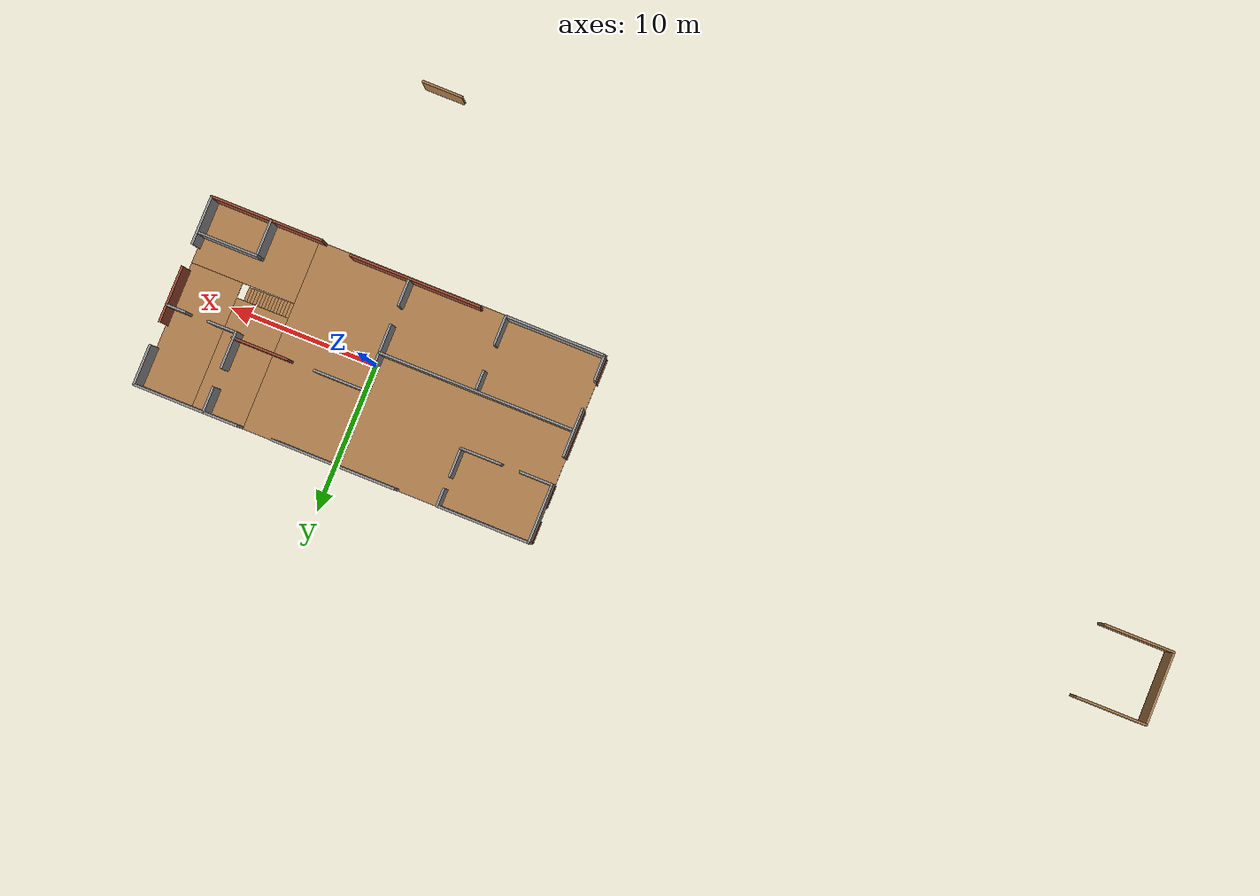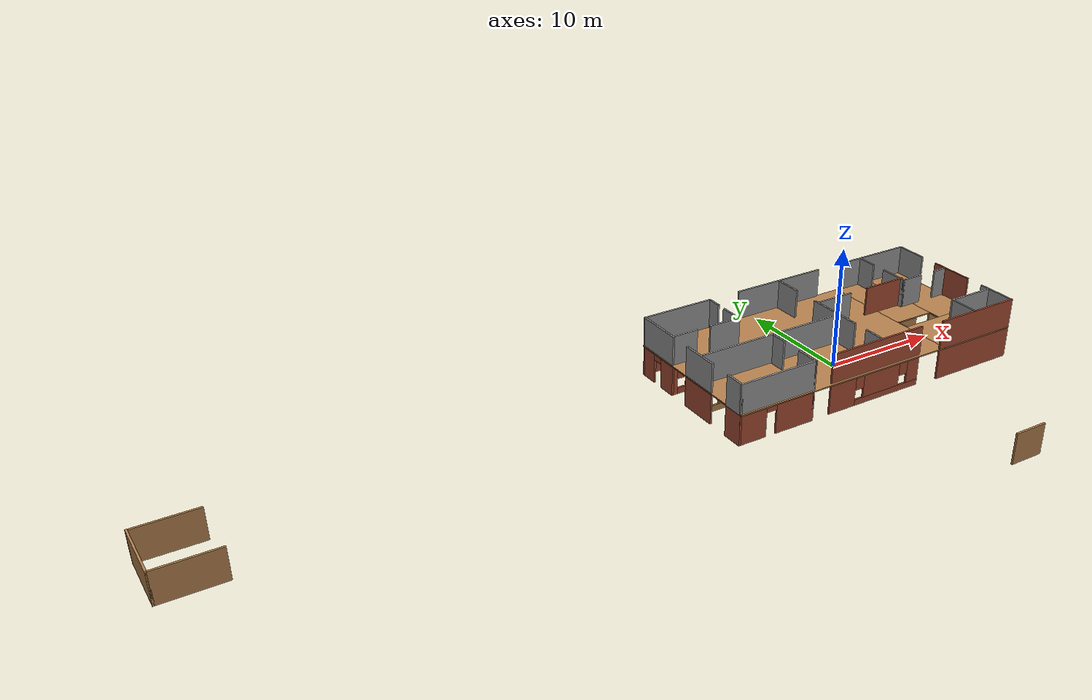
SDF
<?xml version='1.0'?>
<sdf version='1.7'>
  <model name='new_world'>
    <pose>-20.2616 -5.49182 0 0 -0 0</pose>
    <link name='Floor_3'>
      <pose>19.9287 5.96658 2.5 0 -0 0</pose>
      <visual name='Floor_3_Visual_0'>
        <pose>-3.49208 0 0.05 0 -0 0</pose>
        <geometry>
          <box>
            <size>19.5667 12.7728 0.1</size>
          </box>
        </geometry>
        <material>
          <script>
            <uri>file://media/materials/scripts/gazebo.material</uri>
            <name>Gazebo/Wood</name>
          </script>
          <ambient>1 1 1 1</ambient>
        </material>
        <meta>
          <layer>1</layer>
        </meta>
      </visual>
      <collision name='Floor_3_Collision_0'>
        <geometry>
          <box>
            <size>19.5667 12.7728 0.1</size>
          </box>
        </geometry>
        <pose>-3.49208 0 0.05 0 -0 0</pose>
      </collision>
      <visual name='Floor_3_Visual_1'>
        <pose>9.78335 -4.25673 0.05 0 -0 0</pose>
        <geometry>
          <box>
            <size>6.98416 4.25935 0.1</size>
          </box>
        </geometry>
        <material>
          <script>
            <uri>file://media/materials/scripts/gazebo.material</uri>
            <name>Gazebo/Wood</name>
          </script>
          <ambient>1 1 1 1</ambient>
        </material>
        <meta>
          <layer>1</layer>
        </meta>
      </visual>
      <collision name='Floor_3_Collision_1'>
        <geometry>
          <box>
            <size>6.98416 4.25935 0.1</size>
          </box>
        </geometry>
        <pose>9.78335 -4.25673 0.05 0 -0 0</pose>
      </collision>
      <visual name='Floor_3_Visual_2'>
        <pose>11.5333 2.12967 0.05 0 -0 0</pose>
        <geometry>
          <box>
            <size>3.48416 8.51345 0.1</size>
          </box>
        </geometry>
        <material>
          <script>
            <uri>file://media/materials/scripts/gazebo.material</uri>
            <name>Gazebo/Wood</name>
          </script>
          <ambient>1 1 1 1</ambient>
        </material>
        <meta>
          <layer>1</layer>
        </meta>
      </visual>
      <collision name='Floor_3_Collision_2'>
        <geometry>
          <box>
            <size>3.48416 8.51345 0.1</size>
          </box>
        </geometry>
        <pose>11.5333 2.12967 0.05 0 -0 0</pose>
      </collision>
      <visual name='Floor_3_Visual_3'>
        <pose>8.04127 2.62967 0.05 0 -0 0</pose>
        <geometry>
          <box>
            <size>3.5 7.51345 0.1</size>
          </box>
        </geometry>
        <material>
          <script>
            <uri>file://media/materials/scripts/gazebo.material</uri>
            <name>Gazebo/Wood</name>
          </script>
          <ambient>1 1 1 1</ambient>
        </material>
        <meta>
          <layer>1</layer>
        </meta>
      </visual>
      <collision name='Floor_3_Collision_3'>
        <geometry>
          <box>
            <size>3.5 7.51345 0.1</size>
          </box>
        </geometry>
        <pose>8.04127 2.62967 0.05 0 -0 0</pose>
      </collision>
    </link>
    <link name='Stairs_4'>
      <visual name='Stairs_4_Visual_0'>
        <pose>29.6033 4.33952 0.083333 0 -0 -1.5708</pose>
        <geometry>
          <box>
            <size>1 0.233333 0.166667</size>
          </box>
        </geometry>
        <material>
          <script>
            <uri>file://media/materials/scripts/gazebo.material</uri>
            <name>Gazebo/Wood</name>
          </script>
          <ambient>1 1 1 1</ambient>
        </material>
        <meta>
          <layer>0</layer>
        </meta>
      </visual>
      <collision name='Stairs_4_Collision_0'>
        <geometry>
          <box>
            <size>1 0.233333 0.166667</size>
          </box>
        </geometry>
        <pose>29.6033 4.33952 0.083333 0 -0 -1.5708</pose>
      </collision>
      <visual name='Stairs_4_Visual_1'>
        <pose>29.3699 4.33952 0.25 0 -0 -1.5708</pose>
        <geometry>
          <box>
            <size>1 0.233333 0.166667</size>
          </box>
        </geometry>
        <material>
          <script>
            <uri>file://media/materials/scripts/gazebo.material</uri>
            <name>Gazebo/Wood</name>
          </script>
          <ambient>1 1 1 1</ambient>
        </material>
        <meta>
          <layer>0</layer>
        </meta>
      </visual>
      <collision name='Stairs_4_Collision_1'>
        <geometry>
          <box>
            <size>1 0.233333 0.166667</size>
          </box>
        </geometry>
        <pose>29.3699 4.33952 0.25 0 -0 -1.5708</pose>
      </collision>
      <visual name='Stairs_4_Visual_2'>
        <pose>29.1366 4.33952 0.416667 0 -0 -1.5708</pose>
        <geometry>
          <box>
            <size>1 0.233333 0.166667</size>
          </box>
        </geometry>
        <material>
          <script>
            <uri>file://media/materials/scripts/gazebo.material</uri>
            <name>Gazebo/Wood</name>
          </script>
          <ambient>1 1 1 1</ambient>
        </material>
        <meta>
          <layer>0</layer>
        </meta>
      </visual>
      <collision name='Stairs_4_Collision_2'>
        <geometry>
          <box>
            <size>1 0.233333 0.166667</size>
          </box>
        </geometry>
        <pose>29.1366 4.33952 0.416667 0 -0 -1.5708</pose>
      </collision>
      <visual name='Stairs_4_Visual_3'>
        <pose>28.9033 4.33952 0.583333 0 -0 -1.5708</pose>
        <geometry>
          <box>
            <size>1 0.233333 0.166667</size>
          </box>
        </geometry>
        <material>
          <script>
            <uri>file://media/materials/scripts/gazebo.material</uri>
            <name>Gazebo/Wood</name>
          </script>
          <ambient>1 1 1 1</ambient>
        </material>
        <meta>
          <layer>0</layer>
        </meta>
      </visual>
      <collision name='Stairs_4_Collision_3'>
        <geometry>
          <box>
            <size>1 0.233333 0.166667</size>
          </box>
        </geometry>
        <pose>28.9033 4.33952 0.583333 0 -0 -1.5708</pose>
      </collision>
      <visual name='Stairs_4_Visual_4'>
        <pose>28.6699 4.33952 0.75 0 -0 -1.5708</pose>
        <geometry>
          <box>
            <size>1 0.233333 0.166667</size>
          </box>
        </geometry>
        <material>
          <script>
            <uri>file://media/materials/scripts/gazebo.material</uri>
            <name>Gazebo/Wood</name>
          </script>
          <ambient>1 1 1 1</ambient>
        </material>
        <meta>
          <layer>0</layer>
        </meta>
      </visual>
      <collision name='Stairs_4_Collision_4'>
        <geometry>
          <box>
            <size>1 0.233333 0.166667</size>
          </box>
        </geometry>
        <pose>28.6699 4.33952 0.75 0 -0 -1.5708</pose>
      </collision>
      <visual name='Stairs_4_Visual_5'>
        <pose>28.4366 4.33952 0.916667 0 -0 -1.5708</pose>
        <geometry>
          <box>
            <size>1 0.233333 0.166667</size>
          </box>
        </geometry>
        <material>
          <script>
            <uri>file://media/materials/scripts/gazebo.material</uri>
            <name>Gazebo/Wood</name>
          </script>
          <ambient>1 1 1 1</ambient>
        </material>
        <meta>
          <layer>0</layer>
        </meta>
      </visual>
      <collision name='Stairs_4_Collision_5'>
        <geometry>
          <box>
            <size>1 0.233333 0.166667</size>
          </box>
        </geometry>
        <pose>28.4366 4.33952 0.916667 0 -0 -1.5708</pose>
      </collision>
      <visual name='Stairs_4_Visual_6'>
        <pose>28.2033 4.33952 1.08333 0 -0 -1.5708</pose>
        <geometry>
          <box>
            <size>1 0.233333 0.166667</size>
          </box>
        </geometry>
        <material>
          <script>
            <uri>file://media/materials/scripts/gazebo.material</uri>
            <name>Gazebo/Wood</name>
          </script>
          <ambient>1 1 1 1</ambient>
        </material>
        <meta>
          <layer>0</layer>
        </meta>
      </visual>
      <collision name='Stairs_4_Collision_6'>
        <geometry>
          <box>
            <size>1 0.233333 0.166667</size>
          </box>
        </geometry>
        <pose>28.2033 4.33952 1.08333 0 -0 -1.5708</pose>
      </collision>
      <visual name='Stairs_4_Visual_7'>
        <pose>27.9699 4.33952 1.25 0 -0 -1.5708</pose>
        <geometry>
          <box>
            <size>1 0.233333 0.166667</size>
          </box>
        </geometry>
        <material>
          <script>
            <uri>file://media/materials/scripts/gazebo.material</uri>
            <name>Gazebo/Wood</name>
          </script>
          <ambient>1 1 1 1</ambient>
        </material>
        <meta>
          <layer>0</layer>
        </meta>
      </visual>
      <collision name='Stairs_4_Collision_7'>
        <geometry>
          <box>
            <size>1 0.233333 0.166667</size>
          </box>
        </geometry>
        <pose>27.9699 4.33952 1.25 0 -0 -1.5708</pose>
      </collision>
      <visual name='Stairs_4_Visual_8'>
        <pose>27.7366 4.33952 1.41667 0 -0 -1.5708</pose>
        <geometry>
          <box>
            <size>1 0.233333 0.166667</size>
          </box>
        </geometry>
        <material>
          <script>
            <uri>file://media/materials/scripts/gazebo.material</uri>
            <name>Gazebo/Wood</name>
          </script>
          <ambient>1 1 1 1</ambient>
        </material>
        <meta>
          <layer>0</layer>
        </meta>
      </visual>
      <collision name='Stairs_4_Collision_8'>
        <geometry>
          <box>
            <size>1 0.233333 0.166667</size>
          </box>
        </geometry>
        <pose>27.7366 4.33952 1.41667 0 -0 -1.5708</pose>
      </collision>
      <visual name='Stairs_4_Visual_9'>
        <pose>27.5033 4.33952 1.58333 0 -0 -1.5708</pose>
        <geometry>
          <box>
            <size>1 0.233333 0.166667</size>
          </box>
        </geometry>
        <material>
          <script>
            <uri>file://media/materials/scripts/gazebo.material</uri>
            <name>Gazebo/Wood</name>
          </script>
          <ambient>1 1 1 1</ambient>
        </material>
        <meta>
          <layer>0</layer>
        </meta>
      </visual>
      <collision name='Stairs_4_Collision_9'>
        <geometry>
          <box>
            <size>1 0.233333 0.166667</size>
          </box>
        </geometry>
        <pose>27.5033 4.33952 1.58333 0 -0 -1.5708</pose>
      </collision>
      <visual name='Stairs_4_Visual_10'>
        <pose>27.2699 4.33952 1.75 0 -0 -1.5708</pose>
        <geometry>
          <box>
            <size>1 0.233333 0.166667</size>
          </box>
        </geometry>
        <material>
          <script>
            <uri>file://media/materials/scripts/gazebo.material</uri>
            <name>Gazebo/Wood</name>
          </script>
          <ambient>1 1 1 1</ambient>
        </material>
        <meta>
          <layer>0</layer>
        </meta>
      </visual>
      <collision name='Stairs_4_Collision_10'>
        <geometry>
          <box>
            <size>1 0.233333 0.166667</size>
          </box>
        </geometry>
        <pose>27.2699 4.33952 1.75 0 -0 -1.5708</pose>
      </collision>
      <visual name='Stairs_4_Visual_11'>
        <pose>27.0366 4.33952 1.91667 0 -0 -1.5708</pose>
        <geometry>
          <box>
            <size>1 0.233333 0.166667</size>
          </box>
        </geometry>
        <material>
          <script>
            <uri>file://media/materials/scripts/gazebo.material</uri>
            <name>Gazebo/Wood</name>
          </script>
          <ambient>1 1 1 1</ambient>
        </material>
        <meta>
          <layer>0</layer>
        </meta>
      </visual>
      <collision name='Stairs_4_Collision_11'>
        <geometry>
          <box>
            <size>1 0.233333 0.166667</size>
          </box>
        </geometry>
        <pose>27.0366 4.33952 1.91667 0 -0 -1.5708</pose>
      </collision>
      <visual name='Stairs_4_Visual_12'>
        <pose>26.8033 4.33952 2.08333 0 -0 -1.5708</pose>
        <geometry>
          <box>
            <size>1 0.233333 0.166667</size>
          </box>
        </geometry>
        <material>
          <script>
            <uri>file://media/materials/scripts/gazebo.material</uri>
            <name>Gazebo/Wood</name>
          </script>
          <ambient>1 1 1 1</ambient>
        </material>
        <meta>
          <layer>0</layer>
        </meta>
      </visual>
      <collision name='Stairs_4_Collision_12'>
        <geometry>
          <box>
            <size>1 0.233333 0.166667</size>
          </box>
        </geometry>
        <pose>26.8033 4.33952 2.08333 0 -0 -1.5708</pose>
      </collision>
      <visual name='Stairs_4_Visual_13'>
        <pose>26.5699 4.33952 2.25 0 -0 -1.5708</pose>
        <geometry>
          <box>
            <size>1 0.233333 0.166667</size>
          </box>
        </geometry>
        <material>
          <script>
            <uri>file://media/materials/scripts/gazebo.material</uri>
            <name>Gazebo/Wood</name>
          </script>
          <ambient>1 1 1 1</ambient>
        </material>
        <meta>
          <layer>0</layer>
        </meta>
      </visual>
      <collision name='Stairs_4_Collision_13'>
        <geometry>
          <box>
            <size>1 0.233333 0.166667</size>
          </box>
        </geometry>
        <pose>26.5699 4.33952 2.25 0 -0 -1.5708</pose>
      </collision>
      <visual name='Stairs_4_Visual_14'>
        <pose>26.3366 4.33952 2.41667 0 -0 -1.5708</pose>
        <geometry>
          <box>
            <size>1 0.233333 0.166667</size>
          </box>
        </geometry>
        <material>
          <script>
            <uri>file://media/materials/scripts/gazebo.material</uri>
            <name>Gazebo/Wood</name>
          </script>
          <ambient>1 1 1 1</ambient>
        </material>
        <meta>
          <layer>0</layer>
        </meta>
      </visual>
      <collision name='Stairs_4_Collision_14'>
        <geometry>
          <box>
            <size>1 0.233333 0.166667</size>
          </box>
        </geometry>
        <pose>26.3366 4.33952 2.41667 0 -0 -1.5708</pose>
      </collision>
    </link>
    <link name='Wall_15'>
      <pose>9.82012 12.272 0 0 -0 0</pose>
      <visual name='Wall_15_Visual_0'>
        <pose>-1.65398 0 1.25 0 -0 0</pose>
        <geometry>
          <box>
            <size>2.94205 0.15 2.5</size>
          </box>
        </geometry>
        <material>
          <script>
            <uri>file://media/materials/scripts/gazebo.material</uri>
            <name>Gazebo/Bricks</name>
          </script>
          <ambient>1 1 1 1</ambient>
        </material>
        <meta>
          <layer>0</layer>
        </meta>
      </visual>
      <collision name='Wall_15_Collision_0'>
        <geometry>
          <box>
            <size>2.94205 0.15 2.5</size>
          </box>
        </geometry>
        <pose>-1.65398 0 1.25 0 -0 0</pose>
      </collision>
      <visual name='Wall_15_Visual_1'>
        <pose>1.47102 0 0.25 0 -0 0</pose>
        <geometry>
          <box>
            <size>3.30795 0.15 0.5</size>
          </box>
        </geometry>
        <material>
          <script>
            <uri>file://media/materials/scripts/gazebo.material</uri>
            <name>Gazebo/Bricks</name>
          </script>
          <ambient>1 1 1 1</ambient>
        </material>
        <meta>
          <layer>0</layer>
        </meta>
      </visual>
      <collision name='Wall_15_Collision_1'>
        <geometry>
          <box>
            <size>3.30795 0.15 0.5</size>
          </box>
        </geometry>
        <pose>1.47102 0 0.25 0 -0 0</pose>
      </collision>
      <visual name='Wall_15_Visual_2'>
        <pose>1.87102 0 1.5 0 -0 0</pose>
        <geometry>
          <box>
            <size>2.50795 0.15 2</size>
          </box>
        </geometry>
        <material>
          <script>
            <uri>file://media/materials/scripts/gazebo.material</uri>
            <name>Gazebo/Bricks</name>
          </script>
          <ambient>1 1 1 1</ambient>
        </material>
        <meta>
          <layer>0</layer>
        </meta>
      </visual>
      <collision name='Wall_15_Collision_2'>
        <geometry>
          <box>
            <size>2.50795 0.15 2</size>
          </box>
        </geometry>
        <pose>1.87102 0 1.5 0 -0 0</pose>
      </collision>
      <visual name='Wall_15_Visual_3'>
        <pose>0.217048 0 1.9 0 -0 0</pose>
        <geometry>
          <box>
            <size>0.8 0.15 1.2</size>
          </box>
        </geometry>
        <material>
          <script>
            <uri>file://media/materials/scripts/gazebo.material</uri>
            <name>Gazebo/Bricks</name>
          </script>
          <ambient>1 1 1 1</ambient>
        </material>
        <meta>
          <layer>0</layer>
        </meta>
      </visual>
      <collision name='Wall_15_Collision_3'>
        <geometry>
          <box>
            <size>0.8 0.15 1.2</size>
          </box>
        </geometry>
        <pose>0.217048 0 1.9 0 -0 0</pose>
      </collision>
    </link>
    <link name='Wall_166'>
      <collision name='Wall_166_Collision'>
        <geometry>
          <box>
            <size>6.25 0.15 2.5</size>
          </box>
        </geometry>
        <pose>0 0 1.25 0 -0 0</pose>
      </collision>
      <visual name='Wall_166_Visual'>
        <pose>0 0 1.25 0 -0 0</pose>
        <geometry>
          <box>
            <size>6.25 0.15 2.5</size>
          </box>
        </geometry>
        <material>
          <script>
            <uri>file://media/materials/scripts/gazebo.material</uri>
            <name>Gazebo/Grey</name>
          </script>
          <ambient>1 1 1 1</ambient>
        </material>
        <meta>
          <layer>1</layer>
        </meta>
      </visual>
      <pose>9.82012 12.272 2.5 0 -0 0</pose>
    </link>
    <link name='Wall_167'>
      <collision name='Wall_167_Collision'>
        <geometry>
          <box>
            <size>7.5 0.15 2.5</size>
          </box>
        </geometry>
        <pose>0 0 1.25 0 -0 0</pose>
      </collision>
      <visual name='Wall_167_Visual'>
        <pose>0 0 1.25 0 -0 0</pose>
        <geometry>
          <box>
            <size>7.5 0.15 2.5</size>
          </box>
        </geometry>
        <material>
          <script>
            <uri>file://media/materials/scripts/gazebo.material</uri>
            <name>Gazebo/Bricks</name>
          </script>
          <ambient>1 1 1 1</ambient>
        </material>
        <meta>
          <layer>1</layer>
        </meta>
      </visual>
      <pose>29.4319 -0.344823 2.5 0 -0 0</pose>
    </link>
    <link name='Wall_168'>
      <collision name='Wall_168_Collision'>
        <geometry>
          <box>
            <size>2.75 0.15 2.5</size>
          </box>
        </geometry>
        <pose>0 0 1.25 0 -0 0</pose>
      </collision>
      <visual name='Wall_168_Visual'>
        <pose>0 0 1.25 0 -0 0</pose>
        <geometry>
          <box>
            <size>2.75 0.15 2.5</size>
          </box>
        </geometry>
        <material>
          <script>
            <uri>file://media/materials/scripts/gazebo.material</uri>
            <name>Gazebo/Grey</name>
          </script>
          <ambient>1 1 1 1</ambient>
        </material>
        <meta>
          <layer>1</layer>
        </meta>
      </visual>
      <pose>33.1201 10.972 2.5 0 -0 -1.5708</pose>
    </link>
    <link name='Wall_169'>
      <collision name='Wall_169_Collision'>
        <geometry>
          <box>
            <size>3.75 0.15 2.5</size>
          </box>
        </geometry>
        <pose>0 0 1.25 0 -0 0</pose>
      </collision>
      <visual name='Wall_169_Visual'>
        <pose>0 0 1.25 0 -0 0</pose>
        <geometry>
          <box>
            <size>3.75 0.15 2.5</size>
          </box>
        </geometry>
        <material>
          <script>
            <uri>file://media/materials/scripts/gazebo.material</uri>
            <name>Gazebo/Bricks</name>
          </script>
          <ambient>1 1 1 1</ambient>
        </material>
        <meta>
          <layer>1</layer>
        </meta>
      </visual>
      <pose>33.1291 6.22555 2.5 0 -0 -1.5708</pose>
    </link>
    <link name='Wall_170'>
      <collision name='Wall_170_Collision'>
        <geometry>
          <box>
            <size>3.25 0.15 2.5</size>
          </box>
        </geometry>
        <pose>0 0 1.25 0 -0 0</pose>
      </collision>
      <visual name='Wall_170_Visual'>
        <pose>0 0 1.25 0 -0 0</pose>
        <geometry>
          <box>
            <size>3.25 0.15 2.5</size>
          </box>
        </geometry>
        <material>
          <script>
            <uri>file://media/materials/scripts/gazebo.material</uri>
            <name>Gazebo/Grey</name>
          </script>
          <ambient>1 1 1 1</ambient>
        </material>
        <meta>
          <layer>1</layer>
        </meta>
      </visual>
      <pose>33.1091 1.23835 2.5 0 -0 -1.5708</pose>
    </link>
    <link name='Wall_171'>
      <collision name='Wall_171_Collision'>
        <geometry>
          <box>
            <size>4 0.15 2.5</size>
          </box>
        </geometry>
        <pose>0 0 1.25 0 -0 0</pose>
      </collision>
      <visual name='Wall_171_Visual'>
        <pose>0 0 1.25 0 -0 0</pose>
        <geometry>
          <box>
            <size>4 0.15 2.5</size>
          </box>
        </geometry>
        <material>
          <script>
            <uri>file://media/materials/scripts/gazebo.material</uri>
            <name>Gazebo/Grey</name>
          </script>
          <ambient>1 1 1 1</ambient>
        </material>
        <meta>
          <layer>1</layer>
        </meta>
      </visual>
      <pose>6.77012 10.347 2.5 0 -0 -1.5708</pose>
    </link>
    <link name='Wall_172'>
      <collision name='Wall_172_Collision'>
        <geometry>
          <box>
            <size>3.25 0.15 2.5</size>
          </box>
        </geometry>
        <pose>0 0 1.25 0 -0 0</pose>
      </collision>
      <visual name='Wall_172_Visual'>
        <pose>0 0 1.25 0 -0 0</pose>
        <geometry>
          <box>
            <size>3.25 0.15 2.5</size>
          </box>
        </geometry>
        <material>
          <script>
            <uri>file://media/materials/scripts/gazebo.material</uri>
            <name>Gazebo/Grey</name>
          </script>
          <ambient>1 1 1 1</ambient>
        </material>
        <meta>
          <layer>1</layer>
        </meta>
      </visual>
      <pose>6.75883 4.95214 2.5 0 -0 -1.5708</pose>
    </link>
    <link name='Wall_173'>
      <collision name='Wall_173_Collision'>
        <geometry>
          <box>
            <size>1.75 0.15 2.5</size>
          </box>
        </geometry>
        <pose>0 0 1.25 0 -0 0</pose>
      </collision>
      <visual name='Wall_173_Visual'>
        <pose>0 0 1.25 0 -0 0</pose>
        <geometry>
          <box>
            <size>1.75 0.15 2.5</size>
          </box>
        </geometry>
        <material>
          <script>
            <uri>file://media/materials/scripts/gazebo.material</uri>
            <name>Gazebo/Grey</name>
          </script>
          <ambient>1 1 1 1</ambient>
        </material>
        <meta>
          <layer>1</layer>
        </meta>
      </visual>
      <pose>6.72823 0.593575 2.5 0 -0 -1.5708</pose>
    </link>
    <link name='Wall_174'>
      <collision name='Wall_174_Collision'>
        <geometry>
          <box>
            <size>8.25 0.15 2.5</size>
          </box>
        </geometry>
        <pose>0 0 1.25 0 -0 0</pose>
      </collision>
      <visual name='Wall_174_Visual'>
        <pose>0 0 1.25 0 -0 0</pose>
        <geometry>
          <box>
            <size>8.25 0.15 2.5</size>
          </box>
        </geometry>
        <material>
          <script>
            <uri>file://media/materials/scripts/gazebo.material</uri>
            <name>Gazebo/Grey</name>
          </script>
          <ambient>1 1 1 1</ambient>
        </material>
        <meta>
          <layer>1</layer>
        </meta>
      </visual>
      <pose>19.8006 12.278 2.5 0 -0 0</pose>
    </link>
    <link name='Wall_175'>
      <collision name='Wall_175_Collision'>
        <geometry>
          <box>
            <size>7 0.15 2.5</size>
          </box>
        </geometry>
        <pose>0 0 1.25 0 -0 0</pose>
      </collision>
      <visual name='Wall_175_Visual'>
        <pose>0 0 1.25 0 -0 0</pose>
        <geometry>
          <box>
            <size>7 0.15 2.5</size>
          </box>
        </geometry>
        <material>
          <script>
            <uri>file://media/materials/scripts/gazebo.material</uri>
            <name>Gazebo/Grey</name>
          </script>
          <ambient>1 1 1 1</ambient>
        </material>
        <meta>
          <layer>1</layer>
        </meta>
      </visual>
      <pose>29.6951 12.272 2.5 0 -0 3.14159</pose>
    </link>
    <link name='Wall_176'>
      <collision name='Wall_176_Collision'>
        <geometry>
          <box>
            <size>6.75 0.15 2.5</size>
          </box>
        </geometry>
        <pose>0 0 1.25 0 -0 0</pose>
      </collision>
      <visual name='Wall_176_Visual'>
        <pose>0 0 1.25 0 -0 0</pose>
        <geometry>
          <box>
            <size>6.75 0.15 2.5</size>
          </box>
        </geometry>
        <material>
          <script>
            <uri>file://media/materials/scripts/gazebo.material</uri>
            <name>Gazebo/Grey</name>
          </script>
          <ambient>1 1 1 1</ambient>
        </material>
        <meta>
          <layer>1</layer>
        </meta>
      </visual>
      <pose>10.0282 -0.206425 2.5 0 -0 0</pose>
    </link>
    <link name='Wall_177'>
      <collision name='Wall_177_Collision'>
        <geometry>
          <box>
            <size>8.75 0.15 2.5</size>
          </box>
        </geometry>
        <pose>0 0 1.25 0 -0 0</pose>
      </collision>
      <visual name='Wall_177_Visual'>
        <pose>0 0 1.25 0 -0 0</pose>
        <geometry>
          <box>
            <size>8.75 0.15 2.5</size>
          </box>
        </geometry>
        <material>
          <script>
            <uri>file://media/materials/scripts/gazebo.material</uri>
            <name>Gazebo/Bricks</name>
          </script>
          <ambient>1 1 1 1</ambient>
        </material>
        <meta>
          <layer>1</layer>
        </meta>
      </visual>
      <pose>19.3774 -0.149946 2.5 0 -0 0</pose>
    </link>
    <link name='Wall_178'>
      <collision name='Wall_178_Collision'>
        <geometry>
          <box>
            <size>2.25 0.15 2.5</size>
          </box>
        </geometry>
        <pose>0 0 1.25 0 -0 0</pose>
      </collision>
      <visual name='Wall_178_Visual'>
        <pose>0 0 1.25 0 -0 0</pose>
        <geometry>
          <box>
            <size>2.25 0.15 2.5</size>
          </box>
        </geometry>
        <material>
          <script>
            <uri>file://media/materials/scripts/gazebo.material</uri>
            <name>Gazebo/Grey</name>
          </script>
          <ambient>1 1 1 1</ambient>
        </material>
        <meta>
          <layer>1</layer>
        </meta>
      </visual>
      <pose>7.82012 8.42205 2.5 0 -0 0</pose>
    </link>
    <link name='Wall_179'>
      <collision name='Wall_179_Collision'>
        <geometry>
          <box>
            <size>2 0.15 2.5</size>
          </box>
        </geometry>
        <pose>0 0 1.25 0 -0 0</pose>
      </collision>
      <visual name='Wall_179_Visual'>
        <pose>0 0 1.25 0 -0 0</pose>
        <geometry>
          <box>
            <size>2 0.15 2.5</size>
          </box>
        </geometry>
        <material>
          <script>
            <uri>file://media/materials/scripts/gazebo.material</uri>
            <name>Gazebo/Grey</name>
          </script>
          <ambient>1 1 1 1</ambient>
        </material>
        <meta>
          <layer>1</layer>
        </meta>
      </visual>
      <pose>12.8315 9.36573 2.5 0 -0 1.5708</pose>
    </link>
    <link name='Wall_180'>
      <collision name='Wall_180_Collision'>
        <geometry>
          <box>
            <size>1.25 0.15 2.5</size>
          </box>
        </geometry>
        <pose>0 0 1.25 0 -0 0</pose>
      </collision>
      <visual name='Wall_180_Visual'>
        <pose>0 0 1.25 0 -0 0</pose>
        <geometry>
          <box>
            <size>1.25 0.15 2.5</size>
          </box>
        </geometry>
        <material>
          <script>
            <uri>file://media/materials/scripts/gazebo.material</uri>
            <name>Gazebo/Grey</name>
          </script>
          <ambient>1 1 1 1</ambient>
        </material>
        <meta>
          <layer>1</layer>
        </meta>
      </visual>
      <pose>12.8701 11.722 2.5 0 -0 1.5708</pose>
    </link>
    <link name='Wall_181'>
      <collision name='Wall_181_Collision'>
        <geometry>
          <box>
            <size>2.75 0.15 2.5</size>
          </box>
        </geometry>
        <pose>0 0 1.25 0 -0 0</pose>
      </collision>
      <visual name='Wall_181_Visual'>
        <pose>0 0 1.25 0 -0 0</pose>
        <geometry>
          <box>
            <size>2.75 0.15 2.5</size>
          </box>
        </geometry>
        <material>
          <script>
            <uri>file://media/materials/scripts/gazebo.material</uri>
            <name>Gazebo/Grey</name>
          </script>
          <ambient>1 1 1 1</ambient>
        </material>
        <meta>
          <layer>1</layer>
        </meta>
      </visual>
      <pose>11.5201 8.42205 2.5 0 -0 0</pose>
    </link>
    <link name='Wall_182'>
      <collision name='Wall_182_Collision'>
        <geometry>
          <box>
            <size>13 0.15 2.5</size>
          </box>
        </geometry>
        <pose>0 0 1.25 0 -0 0</pose>
      </collision>
      <visual name='Wall_182_Visual'>
        <pose>0 0 1.25 0 -0 0</pose>
        <geometry>
          <box>
            <size>13 0.15 2.5</size>
          </box>
        </geometry>
        <material>
          <script>
            <uri>file://media/materials/scripts/gazebo.material</uri>
            <name>Gazebo/Grey</name>
          </script>
          <ambient>1 1 1 1</ambient>
        </material>
        <meta>
          <layer>1</layer>
        </meta>
      </visual>
      <pose>13.3384 4.80537 2.5 0 -0 0</pose>
    </link>
    <link name='Wall_183'>
      <collision name='Wall_183_Collision'>
        <geometry>
          <box>
            <size>3 0.15 2.5</size>
          </box>
        </geometry>
        <pose>0 0 1.25 0 -0 0</pose>
      </collision>
      <visual name='Wall_183_Visual'>
        <pose>0 0 1.25 0 -0 0</pose>
        <geometry>
          <box>
            <size>3 0.15 2.5</size>
          </box>
        </geometry>
        <material>
          <script>
            <uri>file://media/materials/scripts/gazebo.material</uri>
            <name>Gazebo/Grey</name>
          </script>
          <ambient>1 1 1 1</ambient>
        </material>
        <meta>
          <layer>1</layer>
        </meta>
      </visual>
      <pose>19.7634 6.23037 2.5 0 -0 1.5708</pose>
    </link>
    <link name='Wall_184'>
      <collision name='Wall_184_Collision'>
        <geometry>
          <box>
            <size>2.25 0.15 2.5</size>
          </box>
        </geometry>
        <pose>0 0 1.25 0 -0 0</pose>
      </collision>
      <visual name='Wall_184_Visual'>
        <pose>0 0 1.25 0 -0 0</pose>
        <geometry>
          <box>
            <size>2.25 0.15 2.5</size>
          </box>
        </geometry>
        <material>
          <script>
            <uri>file://media/materials/scripts/gazebo.material</uri>
            <name>Gazebo/Grey</name>
          </script>
          <ambient>1 1 1 1</ambient>
        </material>
        <meta>
          <layer>1</layer>
        </meta>
      </visual>
      <pose>19.7634 11.0554 2.5 0 -0 1.5708</pose>
    </link>
    <link name='Wall_185'>
      <collision name='Wall_185_Collision'>
        <geometry>
          <box>
            <size>2 0.15 2.5</size>
          </box>
        </geometry>
        <pose>0 0 1.25 0 -0 0</pose>
      </collision>
      <visual name='Wall_185_Visual'>
        <pose>0 0 1.25 0 -0 0</pose>
        <geometry>
          <box>
            <size>2 0.15 2.5</size>
          </box>
        </geometry>
        <material>
          <script>
            <uri>file://media/materials/scripts/gazebo.material</uri>
            <name>Gazebo/Grey</name>
          </script>
          <ambient>1 1 1 1</ambient>
        </material>
        <meta>
          <layer>1</layer>
        </meta>
      </visual>
      <pose>13.3282 0.718575 2.5 0 -0 1.5708</pose>
    </link>
    <link name='Wall_186'>
      <collision name='Wall_186_Collision'>
        <geometry>
          <box>
            <size>1.25 0.15 2.5</size>
          </box>
        </geometry>
        <pose>0 0 1.25 0 -0 0</pose>
      </collision>
      <visual name='Wall_186_Visual'>
        <pose>0 0 1.25 0 -0 0</pose>
        <geometry>
          <box>
            <size>1.25 0.15 2.5</size>
          </box>
        </geometry>
        <material>
          <script>
            <uri>file://media/materials/scripts/gazebo.material</uri>
            <name>Gazebo/Grey</name>
          </script>
          <ambient>1 1 1 1</ambient>
        </material>
        <meta>
          <layer>1</layer>
        </meta>
      </visual>
      <pose>13.3282 4.04357 2.5 0 -0 1.5708</pose>
    </link>
    <link name='Wall_187'>
      <collision name='Wall_187_Collision'>
        <geometry>
          <box>
            <size>2 0.15 2.5</size>
          </box>
        </geometry>
        <pose>0 0 1.25 0 -0 0</pose>
      </collision>
      <visual name='Wall_187_Visual'>
        <pose>0 0 1.25 0 -0 0</pose>
        <geometry>
          <box>
            <size>2 0.15 2.5</size>
          </box>
        </geometry>
        <material>
          <script>
            <uri>file://media/materials/scripts/gazebo.material</uri>
            <name>Gazebo/Grey</name>
          </script>
          <ambient>1 1 1 1</ambient>
        </material>
        <meta>
          <layer>1</layer>
        </meta>
      </visual>
      <pose>19.7634 3.88037 2.5 0 -0 -1.5708</pose>
    </link>
    <link name='Wall_188'>
      <collision name='Wall_188_Collision'>
        <geometry>
          <box>
            <size>1.75 0.15 2.5</size>
          </box>
        </geometry>
        <pose>0 0 1.25 0 -0 0</pose>
      </collision>
      <visual name='Wall_188_Visual'>
        <pose>0 0 1.25 0 -0 0</pose>
        <geometry>
          <box>
            <size>1.75 0.15 2.5</size>
          </box>
        </geometry>
        <material>
          <script>
            <uri>file://media/materials/scripts/gazebo.material</uri>
            <name>Gazebo/Grey</name>
          </script>
          <ambient>1 1 1 1</ambient>
        </material>
        <meta>
          <layer>1</layer>
        </meta>
      </visual>
      <pose>19.7634 0.805366 2.5 0 -0 -1.5708</pose>
    </link>
    <link name='Wall_189'>
      <collision name='Wall_189_Collision'>
        <geometry>
          <box>
            <size>1.75 0.15 2.5</size>
          </box>
        </geometry>
        <pose>0 0 1.25 0 -0 0</pose>
      </collision>
      <visual name='Wall_189_Visual'>
        <pose>0 0 1.25 0 -0 0</pose>
        <geometry>
          <box>
            <size>1.75 0.15 2.5</size>
          </box>
        </geometry>
        <material>
          <script>
            <uri>file://media/materials/scripts/gazebo.material</uri>
            <name>Gazebo/Grey</name>
          </script>
          <ambient>1 1 1 1</ambient>
        </material>
        <meta>
          <layer>1</layer>
        </meta>
      </visual>
      <pose>28.489 11.4409 2.5 0 -0 -1.5708</pose>
    </link>
    <link name='Wall_19'>
      <collision name='Wall_19_Collision'>
        <geometry>
          <box>
            <size>7.5 0.15 2.5</size>
          </box>
        </geometry>
        <pose>0 0 1.25 0 -0 0</pose>
      </collision>
      <visual name='Wall_19_Visual'>
        <pose>0 0 1.25 0 -0 0</pose>
        <geometry>
          <box>
            <size>7.5 0.15 2.5</size>
          </box>
        </geometry>
        <material>
          <script>
            <uri>file://media/materials/scripts/gazebo.material</uri>
            <name>Gazebo/Bricks</name>
          </script>
          <ambient>1 1 1 1</ambient>
        </material>
        <meta>
          <layer>0</layer>
        </meta>
      </visual>
      <pose>29.4316 -0.345181 0 0 -0 0</pose>
    </link>
    <link name='Wall_190'>
      <collision name='Wall_190_Collision'>
        <geometry>
          <box>
            <size>2.5 0.15 2.5</size>
          </box>
        </geometry>
        <pose>0 0 1.25 0 -0 0</pose>
      </collision>
      <visual name='Wall_190_Visual'>
        <pose>0 0 1.25 0 -0 0</pose>
        <geometry>
          <box>
            <size>2.5 0.15 2.5</size>
          </box>
        </geometry>
        <material>
          <script>
            <uri>file://media/materials/scripts/gazebo.material</uri>
            <name>Gazebo/Grey</name>
          </script>
          <ambient>1 1 1 1</ambient>
        </material>
        <meta>
          <layer>1</layer>
        </meta>
      </visual>
      <pose>28.489 8.11594 2.5 0 -0 -1.5708</pose>
    </link>
    <link name='Wall_191'>
      <collision name='Wall_191_Collision'>
        <geometry>
          <box>
            <size>2 0.15 2.5</size>
          </box>
        </geometry>
        <pose>0 0 1.25 0 -0 0</pose>
      </collision>
      <visual name='Wall_191_Visual'>
        <pose>0 0 1.25 0 -0 0</pose>
        <geometry>
          <box>
            <size>2 0.15 2.5</size>
          </box>
        </geometry>
        <material>
          <script>
            <uri>file://media/materials/scripts/gazebo.material</uri>
            <name>Gazebo/Grey</name>
          </script>
          <ambient>1 1 1 1</ambient>
        </material>
        <meta>
          <layer>1</layer>
        </meta>
      </visual>
      <pose>29.414 6.94094 2.5 0 -0 0</pose>
    </link>
    <link name='Wall_192'>
      <collision name='Wall_192_Collision'>
        <geometry>
          <box>
            <size>1.25 0.15 2.5</size>
          </box>
        </geometry>
        <pose>0 0 1.25 0 -0 0</pose>
      </collision>
      <visual name='Wall_192_Visual'>
        <pose>0 0 1.25 0 -0 0</pose>
        <geometry>
          <box>
            <size>1.25 0.15 2.5</size>
          </box>
        </geometry>
        <material>
          <script>
            <uri>file://media/materials/scripts/gazebo.material</uri>
            <name>Gazebo/Grey</name>
          </script>
          <ambient>1 1 1 1</ambient>
        </material>
        <meta>
          <layer>1</layer>
        </meta>
      </visual>
      <pose>32.489 6.94094 2.5 0 -0 0</pose>
    </link>
    <link name='Wall_193'>
      <collision name='Wall_193_Collision'>
        <geometry>
          <box>
            <size>3.4468 0.15 2.5</size>
          </box>
        </geometry>
        <pose>0 0 1.25 0 -0 0</pose>
      </collision>
      <visual name='Wall_193_Visual'>
        <pose>0 0 1.25 0 -0 0</pose>
        <geometry>
          <box>
            <size>3.4468 0.15 2.5</size>
          </box>
        </geometry>
        <material>
          <script>
            <uri>file://media/materials/scripts/gazebo.material</uri>
            <name>Gazebo/Grey</name>
          </script>
          <ambient>1 1 1 1</ambient>
        </material>
        <meta>
          <layer>1</layer>
        </meta>
      </visual>
      <pose>21.4125 7.3199 2.5 0 -0 0</pose>
    </link>
    <link name='Wall_194'>
      <collision name='Wall_194_Collision'>
        <geometry>
          <box>
            <size>3.8032 0.15 2.5</size>
          </box>
        </geometry>
        <pose>0 0 1.25 0 -0 0</pose>
      </collision>
      <visual name='Wall_194_Visual'>
        <pose>0 0 1.25 0 -0 0</pose>
        <geometry>
          <box>
            <size>3.8032 0.15 2.5</size>
          </box>
        </geometry>
        <material>
          <script>
            <uri>file://media/materials/scripts/gazebo.material</uri>
            <name>Gazebo/Bricks</name>
          </script>
          <ambient>1 1 1 1</ambient>
        </material>
        <meta>
          <layer>1</layer>
        </meta>
      </visual>
      <pose>26.7375 7.3199 2.5 0 -0 0</pose>
    </link>
    <link name='Wall_199'>
      <collision name='Wall_199_Collision'>
        <geometry>
          <box>
            <size>4 0.15 2.5</size>
          </box>
        </geometry>
        <pose>0 0 1.25 0 -0 0</pose>
      </collision>
      <visual name='Wall_199_Visual'>
        <pose>0 0 1.25 0 -0 0</pose>
        <geometry>
          <box>
            <size>4 0.15 2.5</size>
          </box>
        </geometry>
        <material>
          <script>
            <uri>file://media/materials/scripts/gazebo.material</uri>
            <name>Gazebo/Grey</name>
          </script>
          <ambient>1 1 1 1</ambient>
        </material>
        <meta>
          <layer>1</layer>
        </meta>
      </visual>
      <pose>31.0314 2.04433 2.5 0 -0 0</pose>
    </link>
    <link name='Wall_200'>
      <collision name='Wall_200_Collision'>
        <geometry>
          <box>
            <size>2.5 0.15 2.5</size>
          </box>
        </geometry>
        <pose>0 0 1.25 0 -0 0</pose>
      </collision>
      <visual name='Wall_200_Visual'>
        <pose>0 0 1.25 0 -0 0</pose>
        <geometry>
          <box>
            <size>2.5 0.15 2.5</size>
          </box>
        </geometry>
        <material>
          <script>
            <uri>file://media/materials/scripts/gazebo.material</uri>
            <name>Gazebo/Grey</name>
          </script>
          <ambient>1 1 1 1</ambient>
        </material>
        <meta>
          <layer>1</layer>
        </meta>
      </visual>
      <pose>29.1064 0.869326 2.5 0 -0 -1.5708</pose>
    </link>
    <link name='Wall_208'>
      <collision name='Wall_208_Collision'>
        <geometry>
          <box>
            <size>2.75 0.15 2.5</size>
          </box>
        </geometry>
        <pose>0 0 1.25 0 -0 0</pose>
      </collision>
      <visual name='Wall_208_Visual'>
        <pose>0 0 1.25 0 -0 0</pose>
        <geometry>
          <box>
            <size>2.75 0.15 2.5</size>
          </box>
        </geometry>
        <material>
          <script>
            <uri>file://media/materials/scripts/gazebo.material</uri>
            <name>Gazebo/Wood</name>
          </script>
          <ambient>1 1 1 1</ambient>
        </material>
        <meta>
          <layer>0</layer>
        </meta>
      </visual>
      <pose>22.7009 -12.278 0 0 -0 0</pose>
    </link>
    <link name='Wall_21'>
      <collision name='Wall_21_Collision'>
        <geometry>
          <box>
            <size>2.75 0.15 2.5</size>
          </box>
        </geometry>
        <pose>0 0 1.25 0 -0 0</pose>
      </collision>
      <visual name='Wall_21_Visual'>
        <pose>0 0 1.25 0 -0 0</pose>
        <geometry>
          <box>
            <size>2.75 0.15 2.5</size>
          </box>
        </geometry>
        <material>
          <script>
            <uri>file://media/materials/scripts/gazebo.material</uri>
            <name>Gazebo/Bricks</name>
          </script>
          <ambient>1 1 1 1</ambient>
        </material>
        <meta>
          <layer>0</layer>
        </meta>
      </visual>
      <pose>33.1201 10.972 0 0 -0 -1.5708</pose>
    </link>
    <link name='Wall_216'>
      <collision name='Wall_216_Collision'>
        <geometry>
          <box>
            <size>4.75 0.15 2.5</size>
          </box>
        </geometry>
        <pose>0 0 1.25 0 -0 0</pose>
      </collision>
      <visual name='Wall_216_Visual'>
        <pose>0 0 1.25 0 -0 0</pose>
        <geometry>
          <box>
            <size>4.75 0.15 2.5</size>
          </box>
        </geometry>
        <material>
          <script>
            <uri>file://media/materials/scripts/gazebo.material</uri>
            <name>Gazebo/Wood</name>
          </script>
          <ambient>1 1 1 1</ambient>
        </material>
        <meta>
          <layer>0</layer>
        </meta>
      </visual>
      <pose>-30.8296 8.53108 0 0 -0 0</pose>
    </link>
    <link name='Wall_218'>
      <collision name='Wall_218_Collision'>
        <geometry>
          <box>
            <size>5 0.15 2.5</size>
          </box>
        </geometry>
        <pose>0 0 1.25 0 -0 0</pose>
      </collision>
      <visual name='Wall_218_Visual'>
        <pose>0 0 1.25 0 -0 0</pose>
        <geometry>
          <box>
            <size>5 0.15 2.5</size>
          </box>
        </geometry>
        <material>
          <script>
            <uri>file://media/materials/scripts/gazebo.material</uri>
            <name>Gazebo/Wood</name>
          </script>
          <ambient>1 1 1 1</ambient>
        </material>
        <meta>
          <layer>0</layer>
        </meta>
      </visual>
      <pose>-33.1296 6.10608 0 0 -0 -1.5708</pose>
    </link>
    <link name='Wall_219'>
      <collision name='Wall_219_Collision'>
        <geometry>
          <box>
            <size>4.75 0.15 2.5</size>
          </box>
        </geometry>
        <pose>0 0 1.25 0 -0 0</pose>
      </collision>
      <visual name='Wall_219_Visual'>
        <pose>0 0 1.25 0 -0 0</pose>
        <geometry>
          <box>
            <size>4.75 0.15 2.5</size>
          </box>
        </geometry>
        <material>
          <script>
            <uri>file://media/materials/scripts/gazebo.material</uri>
            <name>Gazebo/Wood</name>
          </script>
          <ambient>1 1 1 1</ambient>
        </material>
        <meta>
          <layer>0</layer>
        </meta>
      </visual>
      <pose>-30.8296 3.68108 0 0 -0 0</pose>
    </link>
    <link name='Wall_24'>
      <collision name='Wall_24_Collision'>
        <geometry>
          <box>
            <size>3.75 0.15 2.5</size>
          </box>
        </geometry>
        <pose>0 0 1.25 0 -0 0</pose>
      </collision>
      <visual name='Wall_24_Visual'>
        <pose>0 0 1.25 0 -0 0</pose>
        <geometry>
          <box>
            <size>3.75 0.15 2.5</size>
          </box>
        </geometry>
        <material>
          <script>
            <uri>file://media/materials/scripts/gazebo.material</uri>
            <name>Gazebo/Wood</name>
          </script>
          <ambient>1 1 1 1</ambient>
        </material>
        <meta>
          <layer>0</layer>
        </meta>
      </visual>
      <pose>33.1296 6.22582 0 0 -0 -1.5708</pose>
    </link>
    <link name='Wall_26'>
      <collision name='Wall_26_Collision'>
        <geometry>
          <box>
            <size>3.25 0.15 2.5</size>
          </box>
        </geometry>
        <pose>0 0 1.25 0 -0 0</pose>
      </collision>
      <visual name='Wall_26_Visual'>
        <pose>0 0 1.25 0 -0 0</pose>
        <geometry>
          <box>
            <size>3.25 0.15 2.5</size>
          </box>
        </geometry>
        <material>
          <script>
            <uri>file://media/materials/scripts/gazebo.material</uri>
            <name>Gazebo/Bricks</name>
          </script>
          <ambient>1 1 1 1</ambient>
        </material>
        <meta>
          <layer>0</layer>
        </meta>
      </visual>
      <pose>33.1096 1.23882 0 0 -0 -1.5708</pose>
    </link>
    <link name='Wall_28'>
      <pose>6.77012 10.347 0 0 -0 -1.5708</pose>
      <visual name='Wall_28_Visual_0'>
        <pose>-1.22892 0 1.25 0 -0 0</pose>
        <geometry>
          <box>
            <size>1.54216 0.15 2.5</size>
          </box>
        </geometry>
        <material>
          <script>
            <uri>file://media/materials/scripts/gazebo.material</uri>
            <name>Gazebo/Bricks</name>
          </script>
          <ambient>1 1 1 1</ambient>
        </material>
        <meta>
          <layer>0</layer>
        </meta>
      </visual>
      <collision name='Wall_28_Collision_0'>
        <geometry>
          <box>
            <size>1.54216 0.15 2.5</size>
          </box>
        </geometry>
        <pose>-1.22892 0 1.25 0 -0 0</pose>
      </collision>
      <visual name='Wall_28_Visual_1'>
        <pose>1.22108 0 1.25 0 -0 0</pose>
        <geometry>
          <box>
            <size>1.55784 0.15 2.5</size>
          </box>
        </geometry>
        <material>
          <script>
            <uri>file://media/materials/scripts/gazebo.material</uri>
            <name>Gazebo/Bricks</name>
          </script>
          <ambient>1 1 1 1</ambient>
        </material>
        <meta>
          <layer>0</layer>
        </meta>
      </visual>
      <collision name='Wall_28_Collision_1'>
        <geometry>
          <box>
            <size>1.55784 0.15 2.5</size>
          </box>
        </geometry>
        <pose>1.22108 0 1.25 0 -0 0</pose>
      </collision>
      <visual name='Wall_28_Visual_2'>
        <pose>-0.007843 0 2.25 0 -0 0</pose>
        <geometry>
          <box>
            <size>0.9 0.15 0.5</size>
          </box>
        </geometry>
        <material>
          <script>
            <uri>file://media/materials/scripts/gazebo.material</uri>
            <name>Gazebo/Bricks</name>
          </script>
          <ambient>1 1 1 1</ambient>
        </material>
        <meta>
          <layer>0</layer>
        </meta>
      </visual>
      <collision name='Wall_28_Collision_2'>
        <geometry>
          <box>
            <size>0.9 0.15 0.5</size>
          </box>
        </geometry>
        <pose>-0.007843 0 2.25 0 -0 0</pose>
      </collision>
    </link>
    <link name='Wall_30'>
      <collision name='Wall_30_Collision'>
        <geometry>
          <box>
            <size>3.25 0.15 2.5</size>
          </box>
        </geometry>
        <pose>0 0 1.25 0 -0 0</pose>
      </collision>
      <visual name='Wall_30_Visual'>
        <pose>0 0 1.25 0 -0 0</pose>
        <geometry>
          <box>
            <size>3.25 0.15 2.5</size>
          </box>
        </geometry>
        <material>
          <script>
            <uri>file://media/materials/scripts/gazebo.material</uri>
            <name>Gazebo/Bricks</name>
          </script>
          <ambient>1 1 1 1</ambient>
        </material>
        <meta>
          <layer>0</layer>
        </meta>
      </visual>
      <pose>6.75883 4.95214 0 0 -0 -1.5708</pose>
    </link>
    <link name='Wall_32'>
      <collision name='Wall_32_Collision'>
        <geometry>
          <box>
            <size>1.75 0.15 2.5</size>
          </box>
        </geometry>
        <pose>0 0 1.25 0 -0 0</pose>
      </collision>
      <visual name='Wall_32_Visual'>
        <pose>0 0 1.25 0 -0 0</pose>
        <geometry>
          <box>
            <size>1.75 0.15 2.5</size>
          </box>
        </geometry>
        <material>
          <script>
            <uri>file://media/materials/scripts/gazebo.material</uri>
            <name>Gazebo/Bricks</name>
          </script>
          <ambient>1 1 1 1</ambient>
        </material>
        <meta>
          <layer>0</layer>
        </meta>
      </visual>
      <pose>6.72841 0.593697 0 0 -0 -1.57058</pose>
    </link>
    <link name='Wall_34'>
      <collision name='Wall_34_Collision'>
        <geometry>
          <box>
            <size>8.25 0.15 2.5</size>
          </box>
        </geometry>
        <pose>0 0 1.25 0 -0 0</pose>
      </collision>
      <visual name='Wall_34_Visual'>
        <pose>0 0 1.25 0 -0 0</pose>
        <geometry>
          <box>
            <size>8.25 0.15 2.5</size>
          </box>
        </geometry>
        <material>
          <script>
            <uri>file://media/materials/scripts/gazebo.material</uri>
            <name>Gazebo/Wood</name>
          </script>
          <ambient>1 1 1 1</ambient>
        </material>
        <meta>
          <layer>0</layer>
        </meta>
      </visual>
      <pose>19.8006 12.278 0 0 -0 0</pose>
    </link>
    <link name='Wall_40'>
      <collision name='Wall_40_Collision'>
        <geometry>
          <box>
            <size>7 0.15 2.5</size>
          </box>
        </geometry>
        <pose>0 0 1.25 0 -0 0</pose>
      </collision>
      <visual name='Wall_40_Visual'>
        <pose>0 0 1.25 0 -0 0</pose>
        <geometry>
          <box>
            <size>7 0.15 2.5</size>
          </box>
        </geometry>
        <material>
          <script>
            <uri>file://media/materials/scripts/gazebo.material</uri>
            <name>Gazebo/Bricks</name>
          </script>
          <ambient>1 1 1 1</ambient>
        </material>
        <meta>
          <layer>0</layer>
        </meta>
      </visual>
      <pose>29.6951 12.272 0 0 -0 3.14159</pose>
    </link>
    <link name='Wall_43'>
      <pose>10.0286 -0.206181 0 0 -0 0</pose>
      <visual name='Wall_43_Visual_0'>
        <pose>-2.17501 0 1.25 0 -0 0</pose>
        <geometry>
          <box>
            <size>2.39999 0.15 2.5</size>
          </box>
        </geometry>
        <material>
          <script>
            <uri>file://media/materials/scripts/gazebo.material</uri>
            <name>Gazebo/Bricks</name>
          </script>
          <ambient>1 1 1 1</ambient>
        </material>
        <meta>
          <layer>0</layer>
        </meta>
      </visual>
      <collision name='Wall_43_Collision_0'>
        <geometry>
          <box>
            <size>2.39999 0.15 2.5</size>
          </box>
        </geometry>
        <pose>-2.17501 0 1.25 0 -0 0</pose>
      </collision>
      <visual name='Wall_43_Visual_1'>
        <pose>1.65 0 1.25 0 -0 0</pose>
        <geometry>
          <box>
            <size>3.45001 0.15 2.5</size>
          </box>
        </geometry>
        <material>
          <script>
            <uri>file://media/materials/scripts/gazebo.material</uri>
            <name>Gazebo/Bricks</name>
          </script>
          <ambient>1 1 1 1</ambient>
        </material>
        <meta>
          <layer>0</layer>
        </meta>
      </visual>
      <collision name='Wall_43_Collision_1'>
        <geometry>
          <box>
            <size>3.45001 0.15 2.5</size>
          </box>
        </geometry>
        <pose>1.65 0 1.25 0 -0 0</pose>
      </collision>
      <visual name='Wall_43_Visual_2'>
        <pose>-0.525009 0 2.25 0 -0 0</pose>
        <geometry>
          <box>
            <size>0.9 0.15 0.5</size>
          </box>
        </geometry>
        <material>
          <script>
            <uri>file://media/materials/scripts/gazebo.material</uri>
            <name>Gazebo/Bricks</name>
          </script>
          <ambient>1 1 1 1</ambient>
        </material>
        <meta>
          <layer>0</layer>
        </meta>
      </visual>
      <collision name='Wall_43_Collision_2'>
        <geometry>
          <box>
            <size>0.9 0.15 0.5</size>
          </box>
        </geometry>
        <pose>-0.525009 0 2.25 0 -0 0</pose>
      </collision>
    </link>
    <link name='Wall_47'>
      <pose>19.3776 -0.150181 0 0 -0 0</pose>
      <visual name='Wall_47_Visual_0'>
        <pose>-3.14544 0 1.25 0 -0 0</pose>
        <geometry>
          <box>
            <size>2.45912 0.15 2.5</size>
          </box>
        </geometry>
        <material>
          <script>
            <uri>file://media/materials/scripts/gazebo.material</uri>
            <name>Gazebo/Bricks</name>
          </script>
          <ambient>1 1 1 1</ambient>
        </material>
        <meta>
          <layer>0</layer>
        </meta>
      </visual>
      <collision name='Wall_47_Collision_0'>
        <geometry>
          <box>
            <size>2.45912 0.15 2.5</size>
          </box>
        </geometry>
        <pose>-3.14544 0 1.25 0 -0 0</pose>
      </collision>
      <visual name='Wall_47_Visual_1'>
        <pose>1.22956 0 0.25 0 -0 0</pose>
        <geometry>
          <box>
            <size>6.29087 0.15 0.5</size>
          </box>
        </geometry>
        <material>
          <script>
            <uri>file://media/materials/scripts/gazebo.material</uri>
            <name>Gazebo/Bricks</name>
          </script>
          <ambient>1 1 1 1</ambient>
        </material>
        <meta>
          <layer>0</layer>
        </meta>
      </visual>
      <collision name='Wall_47_Collision_1'>
        <geometry>
          <box>
            <size>6.29087 0.15 0.5</size>
          </box>
        </geometry>
        <pose>1.22956 0 0.25 0 -0 0</pose>
      </collision>
      <visual name='Wall_47_Visual_2'>
        <pose>0.646334 0 1.5 0 -0 0</pose>
        <geometry>
          <box>
            <size>3.52442 0.15 2</size>
          </box>
        </geometry>
        <material>
          <script>
            <uri>file://media/materials/scripts/gazebo.material</uri>
            <name>Gazebo/Bricks</name>
          </script>
          <ambient>1 1 1 1</ambient>
        </material>
        <meta>
          <layer>0</layer>
        </meta>
      </visual>
      <collision name='Wall_47_Collision_2'>
        <geometry>
          <box>
            <size>3.52442 0.15 2</size>
          </box>
        </geometry>
        <pose>0.646334 0 1.5 0 -0 0</pose>
      </collision>
      <visual name='Wall_47_Visual_3'>
        <pose>3.79177 0 1.5 0 -0 0</pose>
        <geometry>
          <box>
            <size>1.16646 0.15 2</size>
          </box>
        </geometry>
        <material>
          <script>
            <uri>file://media/materials/scripts/gazebo.material</uri>
            <name>Gazebo/Bricks</name>
          </script>
          <ambient>1 1 1 1</ambient>
        </material>
        <meta>
          <layer>0</layer>
        </meta>
      </visual>
      <collision name='Wall_47_Collision_3'>
        <geometry>
          <box>
            <size>1.16646 0.15 2</size>
          </box>
        </geometry>
        <pose>3.79177 0 1.5 0 -0 0</pose>
      </collision>
      <visual name='Wall_47_Visual_4'>
        <pose>-1.51588 0 1.9 0 -0 0</pose>
        <geometry>
          <box>
            <size>0.8 0.15 1.2</size>
          </box>
        </geometry>
        <material>
          <script>
            <uri>file://media/materials/scripts/gazebo.material</uri>
            <name>Gazebo/Bricks</name>
          </script>
          <ambient>1 1 1 1</ambient>
        </material>
        <meta>
          <layer>0</layer>
        </meta>
      </visual>
      <collision name='Wall_47_Collision_4'>
        <geometry>
          <box>
            <size>0.8 0.15 1.2</size>
          </box>
        </geometry>
        <pose>-1.51588 0 1.9 0 -0 0</pose>
      </collision>
      <visual name='Wall_47_Visual_5'>
        <pose>2.80854 0 1.9 0 -0 0</pose>
        <geometry>
          <box>
            <size>0.8 0.15 1.2</size>
          </box>
        </geometry>
        <material>
          <script>
            <uri>file://media/materials/scripts/gazebo.material</uri>
            <name>Gazebo/Bricks</name>
          </script>
          <ambient>1 1 1 1</ambient>
        </material>
        <meta>
          <layer>0</layer>
        </meta>
      </visual>
      <collision name='Wall_47_Collision_5'>
        <geometry>
          <box>
            <size>0.8 0.15 1.2</size>
          </box>
        </geometry>
        <pose>2.80854 0 1.9 0 -0 0</pose>
      </collision>
    </link>
    <link name='Wall_49'>
      <pose>7.82012 8.42205 0 0 -0 0</pose>
      <visual name='Wall_49_Visual_0'>
        <pose>-0.867644 0 1.25 0 -0 0</pose>
        <geometry>
          <box>
            <size>0.514713 0.15 2.5</size>
          </box>
        </geometry>
        <material>
          <script>
            <uri>file://media/materials/scripts/gazebo.material</uri>
            <name>Gazebo/Bricks</name>
          </script>
          <ambient>1 1 1 1</ambient>
        </material>
        <meta>
          <layer>0</layer>
        </meta>
      </visual>
      <collision name='Wall_49_Collision_0'>
        <geometry>
          <box>
            <size>0.514713 0.15 2.5</size>
          </box>
        </geometry>
        <pose>-0.867644 0 1.25 0 -0 0</pose>
      </collision>
      <visual name='Wall_49_Visual_1'>
        <pose>0.257356 0 0.25 0 -0 0</pose>
        <geometry>
          <box>
            <size>1.73529 0.15 0.5</size>
          </box>
        </geometry>
        <material>
          <script>
            <uri>file://media/materials/scripts/gazebo.material</uri>
            <name>Gazebo/Bricks</name>
          </script>
          <ambient>1 1 1 1</ambient>
        </material>
        <meta>
          <layer>0</layer>
        </meta>
      </visual>
      <collision name='Wall_49_Collision_1'>
        <geometry>
          <box>
            <size>1.73529 0.15 0.5</size>
          </box>
        </geometry>
        <pose>0.257356 0 0.25 0 -0 0</pose>
      </collision>
      <visual name='Wall_49_Visual_2'>
        <pose>0.657356 0 1.5 0 -0 0</pose>
        <geometry>
          <box>
            <size>0.935287 0.15 2</size>
          </box>
        </geometry>
        <material>
          <script>
            <uri>file://media/materials/scripts/gazebo.material</uri>
            <name>Gazebo/Bricks</name>
          </script>
          <ambient>1 1 1 1</ambient>
        </material>
        <meta>
          <layer>0</layer>
        </meta>
      </visual>
      <collision name='Wall_49_Collision_2'>
        <geometry>
          <box>
            <size>0.935287 0.15 2</size>
          </box>
        </geometry>
        <pose>0.657356 0 1.5 0 -0 0</pose>
      </collision>
      <visual name='Wall_49_Visual_3'>
        <pose>-0.210287 0 1.9 0 -0 0</pose>
        <geometry>
          <box>
            <size>0.8 0.15 1.2</size>
          </box>
        </geometry>
        <material>
          <script>
            <uri>file://media/materials/scripts/gazebo.material</uri>
            <name>Gazebo/Bricks</name>
          </script>
          <ambient>1 1 1 1</ambient>
        </material>
        <meta>
          <layer>0</layer>
        </meta>
      </visual>
      <collision name='Wall_49_Collision_3'>
        <geometry>
          <box>
            <size>0.8 0.15 1.2</size>
          </box>
        </geometry>
        <pose>-0.210287 0 1.9 0 -0 0</pose>
      </collision>
    </link>
    <link name='Wall_53'>
      <pose>12.8315 9.36573 0 0 -0 1.5708</pose>
      <visual name='Wall_53_Visual_0'>
        <pose>-0.776787 0 1.25 0 -0 0</pose>
        <geometry>
          <box>
            <size>0.446426 0.15 2.5</size>
          </box>
        </geometry>
        <material>
          <script>
            <uri>file://media/materials/scripts/gazebo.material</uri>
            <name>Gazebo/Bricks</name>
          </script>
          <ambient>1 1 1 1</ambient>
        </material>
        <meta>
          <layer>0</layer>
        </meta>
      </visual>
      <collision name='Wall_53_Collision_0'>
        <geometry>
          <box>
            <size>0.446426 0.15 2.5</size>
          </box>
        </geometry>
        <pose>-0.776787 0 1.25 0 -0 0</pose>
      </collision>
      <visual name='Wall_53_Visual_1'>
        <pose>0.223213 0 0.25 0 -0 0</pose>
        <geometry>
          <box>
            <size>1.55357 0.15 0.5</size>
          </box>
        </geometry>
        <material>
          <script>
            <uri>file://media/materials/scripts/gazebo.material</uri>
            <name>Gazebo/Bricks</name>
          </script>
          <ambient>1 1 1 1</ambient>
        </material>
        <meta>
          <layer>0</layer>
        </meta>
      </visual>
      <collision name='Wall_53_Collision_1'>
        <geometry>
          <box>
            <size>1.55357 0.15 0.5</size>
          </box>
        </geometry>
        <pose>0.223213 0 0.25 0 -0 0</pose>
      </collision>
      <visual name='Wall_53_Visual_2'>
        <pose>0.623213 0 1.5 0 -0 0</pose>
        <geometry>
          <box>
            <size>0.753574 0.15 2</size>
          </box>
        </geometry>
        <material>
          <script>
            <uri>file://media/materials/scripts/gazebo.material</uri>
            <name>Gazebo/Bricks</name>
          </script>
          <ambient>1 1 1 1</ambient>
        </material>
        <meta>
          <layer>0</layer>
        </meta>
      </visual>
      <collision name='Wall_53_Collision_2'>
        <geometry>
          <box>
            <size>0.753574 0.15 2</size>
          </box>
        </geometry>
        <pose>0.623213 0 1.5 0 -0 0</pose>
      </collision>
      <visual name='Wall_53_Visual_3'>
        <pose>-0.153574 0 1.9 0 -0 0</pose>
        <geometry>
          <box>
            <size>0.8 0.15 1.2</size>
          </box>
        </geometry>
        <material>
          <script>
            <uri>file://media/materials/scripts/gazebo.material</uri>
            <name>Gazebo/Bricks</name>
          </script>
          <ambient>1 1 1 1</ambient>
        </material>
        <meta>
          <layer>0</layer>
        </meta>
      </visual>
      <collision name='Wall_53_Collision_3'>
        <geometry>
          <box>
            <size>0.8 0.15 1.2</size>
          </box>
        </geometry>
        <pose>-0.153574 0 1.9 0 -0 0</pose>
      </collision>
    </link>
    <link name='Wall_55'>
      <collision name='Wall_55_Collision'>
        <geometry>
          <box>
            <size>1.25 0.15 2.5</size>
          </box>
        </geometry>
        <pose>0 0 1.25 0 -0 0</pose>
      </collision>
      <visual name='Wall_55_Visual'>
        <pose>0 0 1.25 0 -0 0</pose>
        <geometry>
          <box>
            <size>1.25 0.15 2.5</size>
          </box>
        </geometry>
        <material>
          <script>
            <uri>file://media/materials/scripts/gazebo.material</uri>
            <name>Gazebo/Bricks</name>
          </script>
          <ambient>1 1 1 1</ambient>
        </material>
        <meta>
          <layer>0</layer>
        </meta>
      </visual>
      <pose>12.8701 11.722 0 0 -0 1.5708</pose>
    </link>
    <link name='Wall_58'>
      <pose>11.5201 8.42205 0 0 -0 0</pose>
      <visual name='Wall_58_Visual_0'>
        <pose>-1.01335 0 1.25 0 -0 0</pose>
        <geometry>
          <box>
            <size>0.723304 0.15 2.5</size>
          </box>
        </geometry>
        <material>
          <script>
            <uri>file://media/materials/scripts/gazebo.material</uri>
            <name>Gazebo/Bricks</name>
          </script>
          <ambient>1 1 1 1</ambient>
        </material>
        <meta>
          <layer>0</layer>
        </meta>
      </visual>
      <collision name='Wall_58_Collision_0'>
        <geometry>
          <box>
            <size>0.723304 0.15 2.5</size>
          </box>
        </geometry>
        <pose>-1.01335 0 1.25 0 -0 0</pose>
      </collision>
      <visual name='Wall_58_Visual_1'>
        <pose>0.361652 0 0.25 0 -0 0</pose>
        <geometry>
          <box>
            <size>2.0267 0.15 0.5</size>
          </box>
        </geometry>
        <material>
          <script>
            <uri>file://media/materials/scripts/gazebo.material</uri>
            <name>Gazebo/Bricks</name>
          </script>
          <ambient>1 1 1 1</ambient>
        </material>
        <meta>
          <layer>0</layer>
        </meta>
      </visual>
      <collision name='Wall_58_Collision_1'>
        <geometry>
          <box>
            <size>2.0267 0.15 0.5</size>
          </box>
        </geometry>
        <pose>0.361652 0 0.25 0 -0 0</pose>
      </collision>
      <visual name='Wall_58_Visual_2'>
        <pose>0.761652 0 1.5 0 -0 0</pose>
        <geometry>
          <box>
            <size>1.2267 0.15 2</size>
          </box>
        </geometry>
        <material>
          <script>
            <uri>file://media/materials/scripts/gazebo.material</uri>
            <name>Gazebo/Bricks</name>
          </script>
          <ambient>1 1 1 1</ambient>
        </material>
        <meta>
          <layer>0</layer>
        </meta>
      </visual>
      <collision name='Wall_58_Collision_2'>
        <geometry>
          <box>
            <size>1.2267 0.15 2</size>
          </box>
        </geometry>
        <pose>0.761652 0 1.5 0 -0 0</pose>
      </collision>
      <visual name='Wall_58_Visual_3'>
        <pose>-0.251696 0 1.9 0 -0 0</pose>
        <geometry>
          <box>
            <size>0.8 0.15 1.2</size>
          </box>
        </geometry>
        <material>
          <script>
            <uri>file://media/materials/scripts/gazebo.material</uri>
            <name>Gazebo/Bricks</name>
          </script>
          <ambient>1 1 1 1</ambient>
        </material>
        <meta>
          <layer>0</layer>
        </meta>
      </visual>
      <collision name='Wall_58_Collision_3'>
        <geometry>
          <box>
            <size>0.8 0.15 1.2</size>
          </box>
        </geometry>
        <pose>-0.251696 0 1.9 0 -0 0</pose>
      </collision>
    </link>
    <link name='Wall_60'>
      <pose>13.3386 4.80582 0 0 -0 0</pose>
      <visual name='Wall_60_Visual_0'>
        <pose>-6.08003 0 1.25 0 -0 0</pose>
        <geometry>
          <box>
            <size>0.839951 0.15 2.5</size>
          </box>
        </geometry>
        <material>
          <script>
            <uri>file://media/materials/scripts/gazebo.material</uri>
            <name>Gazebo/Wood</name>
          </script>
          <ambient>1 1 1 1</ambient>
        </material>
        <meta>
          <layer>0</layer>
        </meta>
      </visual>
      <collision name='Wall_60_Collision_0'>
        <geometry>
          <box>
            <size>0.839951 0.15 2.5</size>
          </box>
        </geometry>
        <pose>-6.08003 0 1.25 0 -0 0</pose>
      </collision>
      <visual name='Wall_60_Visual_1'>
        <pose>-0.342281 0 1.25 0 -0 0</pose>
        <geometry>
          <box>
            <size>3.62555 0.15 2.5</size>
          </box>
        </geometry>
        <material>
          <script>
            <uri>file://media/materials/scripts/gazebo.material</uri>
            <name>Gazebo/Wood</name>
          </script>
          <ambient>1 1 1 1</ambient>
        </material>
        <meta>
          <layer>0</layer>
        </meta>
      </visual>
      <collision name='Wall_60_Collision_1'>
        <geometry>
          <box>
            <size>3.62555 0.15 2.5</size>
          </box>
        </geometry>
        <pose>-0.342281 0 1.25 0 -0 0</pose>
      </collision>
      <visual name='Wall_60_Visual_2'>
        <pose>2.73998 0 1.25 0 -0 0</pose>
        <geometry>
          <box>
            <size>0.738972 0.15 2.5</size>
          </box>
        </geometry>
        <material>
          <script>
            <uri>file://media/materials/scripts/gazebo.material</uri>
            <name>Gazebo/Wood</name>
          </script>
          <ambient>1 1 1 1</ambient>
        </material>
        <meta>
          <layer>0</layer>
        </meta>
      </visual>
      <collision name='Wall_60_Collision_2'>
        <geometry>
          <box>
            <size>0.738972 0.15 2.5</size>
          </box>
        </geometry>
        <pose>2.73998 0 1.25 0 -0 0</pose>
      </collision>
      <visual name='Wall_60_Visual_3'>
        <pose>-4.35755 0 0.25 0 -0 0</pose>
        <geometry>
          <box>
            <size>2.60499 0.15 0.5</size>
          </box>
        </geometry>
        <material>
          <script>
            <uri>file://media/materials/scripts/gazebo.material</uri>
            <name>Gazebo/Wood</name>
          </script>
          <ambient>1 1 1 1</ambient>
        </material>
        <meta>
          <layer>0</layer>
        </meta>
      </visual>
      <collision name='Wall_60_Collision_3'>
        <geometry>
          <box>
            <size>2.60499 0.15 0.5</size>
          </box>
        </geometry>
        <pose>-4.35755 0 0.25 0 -0 0</pose>
      </collision>
      <visual name='Wall_60_Visual_4'>
        <pose>4.80473 0 0.25 0 -0 0</pose>
        <geometry>
          <box>
            <size>3.39053 0.15 0.5</size>
          </box>
        </geometry>
        <material>
          <script>
            <uri>file://media/materials/scripts/gazebo.material</uri>
            <name>Gazebo/Wood</name>
          </script>
          <ambient>1 1 1 1</ambient>
        </material>
        <meta>
          <layer>0</layer>
        </meta>
      </visual>
      <collision name='Wall_60_Collision_4'>
        <geometry>
          <box>
            <size>3.39053 0.15 0.5</size>
          </box>
        </geometry>
        <pose>4.80473 0 0.25 0 -0 0</pose>
      </collision>
      <visual name='Wall_60_Visual_5'>
        <pose>-3.95755 0 1.5 0 -0 0</pose>
        <geometry>
          <box>
            <size>1.80499 0.15 2</size>
          </box>
        </geometry>
        <material>
          <script>
            <uri>file://media/materials/scripts/gazebo.material</uri>
            <name>Gazebo/Wood</name>
          </script>
          <ambient>1 1 1 1</ambient>
        </material>
        <meta>
          <layer>0</layer>
        </meta>
      </visual>
      <collision name='Wall_60_Collision_5'>
        <geometry>
          <box>
            <size>1.80499 0.15 2</size>
          </box>
        </geometry>
        <pose>-3.95755 0 1.5 0 -0 0</pose>
      </collision>
      <visual name='Wall_60_Visual_6'>
        <pose>-3.95755 0 1.5 0 -0 0</pose>
        <geometry>
          <box>
            <size>1.80499 0.15 2</size>
          </box>
        </geometry>
        <material>
          <script>
            <uri>file://media/materials/scripts/gazebo.material</uri>
            <name>Gazebo/Wood</name>
          </script>
          <ambient>1 1 1 1</ambient>
        </material>
        <meta>
          <layer>0</layer>
        </meta>
      </visual>
      <collision name='Wall_60_Collision_6'>
        <geometry>
          <box>
            <size>1.80499 0.15 2</size>
          </box>
        </geometry>
        <pose>-3.95755 0 1.5 0 -0 0</pose>
      </collision>
      <visual name='Wall_60_Visual_7'>
        <pose>5.20473 0 1.5 0 -0 0</pose>
        <geometry>
          <box>
            <size>2.59053 0.15 2</size>
          </box>
        </geometry>
        <material>
          <script>
            <uri>file://media/materials/scripts/gazebo.material</uri>
            <name>Gazebo/Wood</name>
          </script>
          <ambient>1 1 1 1</ambient>
        </material>
        <meta>
          <layer>0</layer>
        </meta>
      </visual>
      <collision name='Wall_60_Collision_7'>
        <geometry>
          <box>
            <size>2.59053 0.15 2</size>
          </box>
        </geometry>
        <pose>5.20473 0 1.5 0 -0 0</pose>
      </collision>
      <visual name='Wall_60_Visual_8'>
        <pose>-5.26005 0 1.9 0 -0 0</pose>
        <geometry>
          <box>
            <size>0.8 0.15 1.2</size>
          </box>
        </geometry>
        <material>
          <script>
            <uri>file://media/materials/scripts/gazebo.material</uri>
            <name>Gazebo/Wood</name>
          </script>
          <ambient>1 1 1 1</ambient>
        </material>
        <meta>
          <layer>0</layer>
        </meta>
      </visual>
      <collision name='Wall_60_Collision_8'>
        <geometry>
          <box>
            <size>0.8 0.15 1.2</size>
          </box>
        </geometry>
        <pose>-5.26005 0 1.9 0 -0 0</pose>
      </collision>
      <visual name='Wall_60_Visual_9'>
        <pose>3.50947 0 1.9 0 -0 0</pose>
        <geometry>
          <box>
            <size>0.8 0.15 1.2</size>
          </box>
        </geometry>
        <material>
          <script>
            <uri>file://media/materials/scripts/gazebo.material</uri>
            <name>Gazebo/Wood</name>
          </script>
          <ambient>1 1 1 1</ambient>
        </material>
        <meta>
          <layer>0</layer>
        </meta>
      </visual>
      <collision name='Wall_60_Collision_9'>
        <geometry>
          <box>
            <size>0.8 0.15 1.2</size>
          </box>
        </geometry>
        <pose>3.50947 0 1.9 0 -0 0</pose>
      </collision>
      <visual name='Wall_60_Visual_10'>
        <pose>1.9205 0 2.25 0 -0 0</pose>
        <geometry>
          <box>
            <size>0.9 0.15 0.5</size>
          </box>
        </geometry>
        <material>
          <script>
            <uri>file://media/materials/scripts/gazebo.material</uri>
            <name>Gazebo/Wood</name>
          </script>
          <ambient>1 1 1 1</ambient>
        </material>
        <meta>
          <layer>0</layer>
        </meta>
      </visual>
      <collision name='Wall_60_Collision_10'>
        <geometry>
          <box>
            <size>0.9 0.15 0.5</size>
          </box>
        </geometry>
        <pose>1.9205 0 2.25 0 -0 0</pose>
      </collision>
      <visual name='Wall_60_Visual_11'>
        <pose>-2.60506 0 2.25 0 -0 0</pose>
        <geometry>
          <box>
            <size>0.9 0.15 0.5</size>
          </box>
        </geometry>
        <material>
          <script>
            <uri>file://media/materials/scripts/gazebo.material</uri>
            <name>Gazebo/Wood</name>
          </script>
          <ambient>1 1 1 1</ambient>
        </material>
        <meta>
          <layer>0</layer>
        </meta>
      </visual>
      <collision name='Wall_60_Collision_11'>
        <geometry>
          <box>
            <size>0.9 0.15 0.5</size>
          </box>
        </geometry>
        <pose>-2.60506 0 2.25 0 -0 0</pose>
      </collision>
      <visual name='Wall_60_Visual_12'>
        <pose>-2.60506 0 2.25 0 -0 0</pose>
        <geometry>
          <box>
            <size>0.9 0.15 0.5</size>
          </box>
        </geometry>
        <material>
          <script>
            <uri>file://media/materials/scripts/gazebo.material</uri>
            <name>Gazebo/Wood</name>
          </script>
          <ambient>1 1 1 1</ambient>
        </material>
        <meta>
          <layer>0</layer>
        </meta>
      </visual>
      <collision name='Wall_60_Collision_12'>
        <geometry>
          <box>
            <size>0.9 0.15 0.5</size>
          </box>
        </geometry>
        <pose>-2.60506 0 2.25 0 -0 0</pose>
      </collision>
    </link>
    <link name='Wall_61'>
      <collision name='Wall_61_Collision'>
        <geometry>
          <box>
            <size>3 0.15 2.5</size>
          </box>
        </geometry>
        <pose>0 0 1.25 0 -0 0</pose>
      </collision>
      <visual name='Wall_61_Visual'>
        <pose>0 0 1.25 0 -0 0</pose>
        <geometry>
          <box>
            <size>3 0.15 2.5</size>
          </box>
        </geometry>
        <material>
          <script>
            <uri>file://media/materials/scripts/gazebo.material</uri>
            <name>Gazebo/Wood</name>
          </script>
          <ambient>1 1 1 1</ambient>
        </material>
        <meta>
          <layer>0</layer>
        </meta>
      </visual>
      <pose>19.7635 6.23059 0 0 -0 1.57088</pose>
    </link>
    <link name='Wall_63'>
      <pose>19.7634 11.0554 0 0 -0 1.5708</pose>
      <visual name='Wall_63_Visual_0'>
        <pose>-0.791187 0 1.25 0 -0 0</pose>
        <geometry>
          <box>
            <size>0.667626 0.15 2.5</size>
          </box>
        </geometry>
        <material>
          <script>
            <uri>file://media/materials/scripts/gazebo.material</uri>
            <name>Gazebo/Wood</name>
          </script>
          <ambient>1 1 1 1</ambient>
        </material>
        <meta>
          <layer>0</layer>
        </meta>
      </visual>
      <collision name='Wall_63_Collision_0'>
        <geometry>
          <box>
            <size>0.667626 0.15 2.5</size>
          </box>
        </geometry>
        <pose>-0.791187 0 1.25 0 -0 0</pose>
      </collision>
      <visual name='Wall_63_Visual_1'>
        <pose>0.333813 0 0.25 0 -0 0</pose>
        <geometry>
          <box>
            <size>1.58237 0.15 0.5</size>
          </box>
        </geometry>
        <material>
          <script>
            <uri>file://media/materials/scripts/gazebo.material</uri>
            <name>Gazebo/Wood</name>
          </script>
          <ambient>1 1 1 1</ambient>
        </material>
        <meta>
          <layer>0</layer>
        </meta>
      </visual>
      <collision name='Wall_63_Collision_1'>
        <geometry>
          <box>
            <size>1.58237 0.15 0.5</size>
          </box>
        </geometry>
        <pose>0.333813 0 0.25 0 -0 0</pose>
      </collision>
      <visual name='Wall_63_Visual_2'>
        <pose>0.733813 0 1.5 0 -0 0</pose>
        <geometry>
          <box>
            <size>0.782374 0.15 2</size>
          </box>
        </geometry>
        <material>
          <script>
            <uri>file://media/materials/scripts/gazebo.material</uri>
            <name>Gazebo/Wood</name>
          </script>
          <ambient>1 1 1 1</ambient>
        </material>
        <meta>
          <layer>0</layer>
        </meta>
      </visual>
      <collision name='Wall_63_Collision_2'>
        <geometry>
          <box>
            <size>0.782374 0.15 2</size>
          </box>
        </geometry>
        <pose>0.733813 0 1.5 0 -0 0</pose>
      </collision>
      <visual name='Wall_63_Visual_3'>
        <pose>-0.057374 0 1.9 0 -0 0</pose>
        <geometry>
          <box>
            <size>0.8 0.15 1.2</size>
          </box>
        </geometry>
        <material>
          <script>
            <uri>file://media/materials/scripts/gazebo.material</uri>
            <name>Gazebo/Wood</name>
          </script>
          <ambient>1 1 1 1</ambient>
        </material>
        <meta>
          <layer>0</layer>
        </meta>
      </visual>
      <collision name='Wall_63_Collision_3'>
        <geometry>
          <box>
            <size>0.8 0.15 1.2</size>
          </box>
        </geometry>
        <pose>-0.057374 0 1.9 0 -0 0</pose>
      </collision>
    </link>
    <link name='Wall_66'>
      <collision name='Wall_66_Collision'>
        <geometry>
          <box>
            <size>2 0.15 2.5</size>
          </box>
        </geometry>
        <pose>0 0 1.25 0 -0 0</pose>
      </collision>
      <visual name='Wall_66_Visual'>
        <pose>0 0 1.25 0 -0 0</pose>
        <geometry>
          <box>
            <size>2 0.15 2.5</size>
          </box>
        </geometry>
        <material>
          <script>
            <uri>file://media/materials/scripts/gazebo.material</uri>
            <name>Gazebo/Bricks</name>
          </script>
          <ambient>1 1 1 1</ambient>
        </material>
        <meta>
          <layer>0</layer>
        </meta>
      </visual>
      <pose>13.3286 0.718819 0 0 -0 1.5708</pose>
    </link>
    <link name='Wall_68'>
      <collision name='Wall_68_Collision'>
        <geometry>
          <box>
            <size>1.25 0.15 2.5</size>
          </box>
        </geometry>
        <pose>0 0 1.25 0 -0 0</pose>
      </collision>
      <visual name='Wall_68_Visual'>
        <pose>0 0 1.25 0 -0 0</pose>
        <geometry>
          <box>
            <size>1.25 0.15 2.5</size>
          </box>
        </geometry>
        <material>
          <script>
            <uri>file://media/materials/scripts/gazebo.material</uri>
            <name>Gazebo/Bricks</name>
          </script>
          <ambient>1 1 1 1</ambient>
        </material>
        <meta>
          <layer>0</layer>
        </meta>
      </visual>
      <pose>13.3282 4.04357 0 0 -0 1.5708</pose>
    </link>
    <link name='Wall_70'>
      <collision name='Wall_70_Collision'>
        <geometry>
          <box>
            <size>2 0.15 2.5</size>
          </box>
        </geometry>
        <pose>0 0 1.25 0 -0 0</pose>
      </collision>
      <visual name='Wall_70_Visual'>
        <pose>0 0 1.25 0 -0 0</pose>
        <geometry>
          <box>
            <size>2 0.15 2.5</size>
          </box>
        </geometry>
        <material>
          <script>
            <uri>file://media/materials/scripts/gazebo.material</uri>
            <name>Gazebo/Wood</name>
          </script>
          <ambient>1 1 1 1</ambient>
        </material>
        <meta>
          <layer>0</layer>
        </meta>
      </visual>
      <pose>19.7635 3.88059 0 0 -0 -1.57092</pose>
    </link>
    <link name='Wall_72'>
      <collision name='Wall_72_Collision'>
        <geometry>
          <box>
            <size>1.75 0.15 2.5</size>
          </box>
        </geometry>
        <pose>0 0 1.25 0 -0 0</pose>
      </collision>
      <visual name='Wall_72_Visual'>
        <pose>0 0 1.25 0 -0 0</pose>
        <geometry>
          <box>
            <size>1.75 0.15 2.5</size>
          </box>
        </geometry>
        <material>
          <script>
            <uri>file://media/materials/scripts/gazebo.material</uri>
            <name>Gazebo/Bricks</name>
          </script>
          <ambient>1 1 1 1</ambient>
        </material>
        <meta>
          <layer>0</layer>
        </meta>
      </visual>
      <pose>19.7636 0.805819 0 0 -0 -1.5708</pose>
    </link>
    <link name='Wall_74'>
      <collision name='Wall_74_Collision'>
        <geometry>
          <box>
            <size>1.75 0.15 2.5</size>
          </box>
        </geometry>
        <pose>0 0 1.25 0 -0 0</pose>
      </collision>
      <visual name='Wall_74_Visual'>
        <pose>0 0 1.25 0 -0 0</pose>
        <geometry>
          <box>
            <size>1.75 0.15 2.5</size>
          </box>
        </geometry>
        <material>
          <script>
            <uri>file://media/materials/scripts/gazebo.material</uri>
            <name>Gazebo/Wood</name>
          </script>
          <ambient>1 1 1 1</ambient>
        </material>
        <meta>
          <layer>0</layer>
        </meta>
      </visual>
      <pose>28.489 11.4409 0 0 -0 -1.5708</pose>
    </link>
    <link name='Wall_76'>
      <collision name='Wall_76_Collision'>
        <geometry>
          <box>
            <size>2.5 0.15 2.5</size>
          </box>
        </geometry>
        <pose>0 0 1.25 0 -0 0</pose>
      </collision>
      <visual name='Wall_76_Visual'>
        <pose>0 0 1.25 0 -0 0</pose>
        <geometry>
          <box>
            <size>2.5 0.15 2.5</size>
          </box>
        </geometry>
        <material>
          <script>
            <uri>file://media/materials/scripts/gazebo.material</uri>
            <name>Gazebo/Bricks</name>
          </script>
          <ambient>1 1 1 1</ambient>
        </material>
        <meta>
          <layer>0</layer>
        </meta>
      </visual>
      <pose>28.489 8.11594 0 0 -0 -1.5708</pose>
    </link>
    <link name='Wall_77'>
      <collision name='Wall_77_Collision'>
        <geometry>
          <box>
            <size>2 0.15 2.5</size>
          </box>
        </geometry>
        <pose>0 0 1.25 0 -0 0</pose>
      </collision>
      <visual name='Wall_77_Visual'>
        <pose>0 0 1.25 0 -0 0</pose>
        <geometry>
          <box>
            <size>2 0.15 2.5</size>
          </box>
        </geometry>
        <material>
          <script>
            <uri>file://media/materials/scripts/gazebo.material</uri>
            <name>Gazebo/Wood</name>
          </script>
          <ambient>1 1 1 1</ambient>
        </material>
        <meta>
          <layer>0</layer>
        </meta>
      </visual>
      <pose>29.414 6.94094 0 0 -0 0</pose>
    </link>
    <link name='Wall_79'>
      <collision name='Wall_79_Collision'>
        <geometry>
          <box>
            <size>1.25 0.15 2.5</size>
          </box>
        </geometry>
        <pose>0 0 1.25 0 -0 0</pose>
      </collision>
      <visual name='Wall_79_Visual'>
        <pose>0 0 1.25 0 -0 0</pose>
        <geometry>
          <box>
            <size>1.25 0.15 2.5</size>
          </box>
        </geometry>
        <material>
          <script>
            <uri>file://media/materials/scripts/gazebo.material</uri>
            <name>Gazebo/Wood</name>
          </script>
          <ambient>1 1 1 1</ambient>
        </material>
        <meta>
          <layer>0</layer>
        </meta>
      </visual>
      <pose>32.489 6.94094 0 0 -0 0</pose>
    </link>
    <link name='Wall_83'>
      <collision name='Wall_83_Collision'>
        <geometry>
          <box>
            <size>3.4468 0.15 2.5</size>
          </box>
        </geometry>
        <pose>0 0 1.25 0 -0 0</pose>
      </collision>
      <visual name='Wall_83_Visual'>
        <pose>0 0 1.25 0 -0 0</pose>
        <geometry>
          <box>
            <size>3.4468 0.15 2.5</size>
          </box>
        </geometry>
        <material>
          <script>
            <uri>file://media/materials/scripts/gazebo.material</uri>
            <name>Gazebo/Wood</name>
          </script>
          <ambient>1 1 1 1</ambient>
        </material>
        <meta>
          <layer>0</layer>
        </meta>
      </visual>
      <pose>21.4125 7.3199 0 0 -0 0</pose>
    </link>
    <link name='Wall_85'>
      <collision name='Wall_85_Collision'>
        <geometry>
          <box>
            <size>3.8032 0.15 2.5</size>
          </box>
        </geometry>
        <pose>0 0 1.25 0 -0 0</pose>
      </collision>
      <visual name='Wall_85_Visual'>
        <pose>0 0 1.25 0 -0 0</pose>
        <geometry>
          <box>
            <size>3.8032 0.15 2.5</size>
          </box>
        </geometry>
        <material>
          <script>
            <uri>file://media/materials/scripts/gazebo.material</uri>
            <name>Gazebo/Bricks</name>
          </script>
          <ambient>1 1 1 1</ambient>
        </material>
        <meta>
          <layer>0</layer>
        </meta>
      </visual>
      <pose>26.7375 7.3199 0 0 -0 0</pose>
    </link>
    <link name='Wall_87'>
      <collision name='Wall_87_Collision'>
        <geometry>
          <box>
            <size>2.5 0.15 2.5</size>
          </box>
        </geometry>
        <pose>0 0 1.25 0 -0 0</pose>
      </collision>
      <visual name='Wall_87_Visual'>
        <pose>0 0 1.25 0 -0 0</pose>
        <geometry>
          <box>
            <size>2.5 0.15 2.5</size>
          </box>
        </geometry>
        <material>
          <script>
            <uri>file://media/materials/scripts/gazebo.material</uri>
            <name>Gazebo/Bricks</name>
          </script>
          <ambient>1 1 1 1</ambient>
        </material>
        <meta>
          <layer>0</layer>
        </meta>
      </visual>
      <pose>23.6307 3.65304 0 0 -0 -1.5708</pose>
    </link>
    <link name='Wall_88'>
      <pose>24.9307 2.47804 0 0 -0 0</pose>
      <visual name='Wall_88_Visual_0'>
        <pose>-0.893527 0 1.25 0 -0 0</pose>
        <geometry>
          <box>
            <size>0.962946 0.15 2.5</size>
          </box>
        </geometry>
        <material>
          <script>
            <uri>file://media/materials/scripts/gazebo.material</uri>
            <name>Gazebo/Wood</name>
          </script>
          <ambient>1 1 1 1</ambient>
        </material>
        <meta>
          <layer>0</layer>
        </meta>
      </visual>
      <collision name='Wall_88_Collision_0'>
        <geometry>
          <box>
            <size>0.962946 0.15 2.5</size>
          </box>
        </geometry>
        <pose>-0.893527 0 1.25 0 -0 0</pose>
      </collision>
      <visual name='Wall_88_Visual_1'>
        <pose>0.931473 0 1.25 0 -0 0</pose>
        <geometry>
          <box>
            <size>0.887054 0.15 2.5</size>
          </box>
        </geometry>
        <material>
          <script>
            <uri>file://media/materials/scripts/gazebo.material</uri>
            <name>Gazebo/Wood</name>
          </script>
          <ambient>1 1 1 1</ambient>
        </material>
        <meta>
          <layer>0</layer>
        </meta>
      </visual>
      <collision name='Wall_88_Collision_1'>
        <geometry>
          <box>
            <size>0.887054 0.15 2.5</size>
          </box>
        </geometry>
        <pose>0.931473 0 1.25 0 -0 0</pose>
      </collision>
      <visual name='Wall_88_Visual_2'>
        <pose>0.037946 0 2.25 0 -0 0</pose>
        <geometry>
          <box>
            <size>0.9 0.15 0.5</size>
          </box>
        </geometry>
        <material>
          <script>
            <uri>file://media/materials/scripts/gazebo.material</uri>
            <name>Gazebo/Wood</name>
          </script>
          <ambient>1 1 1 1</ambient>
        </material>
        <meta>
          <layer>0</layer>
        </meta>
      </visual>
      <collision name='Wall_88_Collision_2'>
        <geometry>
          <box>
            <size>0.9 0.15 0.5</size>
          </box>
        </geometry>
        <pose>0.037946 0 2.25 0 -0 0</pose>
      </collision>
    </link>
    <link name='Wall_89'>
      <collision name='Wall_89_Collision'>
        <geometry>
          <box>
            <size>2.5 0.15 2.5</size>
          </box>
        </geometry>
        <pose>0 0 1.25 0 -0 0</pose>
      </collision>
      <visual name='Wall_89_Visual'>
        <pose>0 0 1.25 0 -0 0</pose>
        <geometry>
          <box>
            <size>2.5 0.15 2.5</size>
          </box>
        </geometry>
        <material>
          <script>
            <uri>file://media/materials/scripts/gazebo.material</uri>
            <name>Gazebo/Wood</name>
          </script>
          <ambient>1 1 1 1</ambient>
        </material>
        <meta>
          <layer>0</layer>
        </meta>
      </visual>
      <pose>26.2307 3.65304 0 0 -0 1.5708</pose>
    </link>
    <link name='Wall_90'>
      <collision name='Wall_90_Collision'>
        <geometry>
          <box>
            <size>2.75 0.15 2.5</size>
          </box>
        </geometry>
        <pose>0 0 1.25 0 -0 0</pose>
      </collision>
      <visual name='Wall_90_Visual'>
        <pose>0 0 1.25 0 -0 0</pose>
        <geometry>
          <box>
            <size>2.75 0.15 2.5</size>
          </box>
        </geometry>
        <material>
          <script>
            <uri>file://media/materials/scripts/gazebo.material</uri>
            <name>Gazebo/Wood</name>
          </script>
          <ambient>1 1 1 1</ambient>
        </material>
        <meta>
          <layer>0</layer>
        </meta>
      </visual>
      <pose>24.9307 4.82804 0 0 -0 3.14159</pose>
    </link>
    <link name='Wall_92'>
      <pose>31.0316 2.04482 0 0 -0 0</pose>
      <visual name='Wall_92_Visual_0'>
        <pose>-1.13224 0 1.25 0 -0 0</pose>
        <geometry>
          <box>
            <size>1.73553 0.15 2.5</size>
          </box>
        </geometry>
        <material>
          <script>
            <uri>file://media/materials/scripts/gazebo.material</uri>
            <name>Gazebo/Wood</name>
          </script>
          <ambient>1 1 1 1</ambient>
        </material>
        <meta>
          <layer>0</layer>
        </meta>
      </visual>
      <collision name='Wall_92_Collision_0'>
        <geometry>
          <box>
            <size>1.73553 0.15 2.5</size>
          </box>
        </geometry>
        <pose>-1.13224 0 1.25 0 -0 0</pose>
      </collision>
      <visual name='Wall_92_Visual_1'>
        <pose>1.31776 0 1.25 0 -0 0</pose>
        <geometry>
          <box>
            <size>1.36447 0.15 2.5</size>
          </box>
        </geometry>
        <material>
          <script>
            <uri>file://media/materials/scripts/gazebo.material</uri>
            <name>Gazebo/Wood</name>
          </script>
          <ambient>1 1 1 1</ambient>
        </material>
        <meta>
          <layer>0</layer>
        </meta>
      </visual>
      <collision name='Wall_92_Collision_1'>
        <geometry>
          <box>
            <size>1.36447 0.15 2.5</size>
          </box>
        </geometry>
        <pose>1.31776 0 1.25 0 -0 0</pose>
      </collision>
      <visual name='Wall_92_Visual_2'>
        <pose>0.185529 0 2.25 0 -0 0</pose>
        <geometry>
          <box>
            <size>0.9 0.15 0.5</size>
          </box>
        </geometry>
        <material>
          <script>
            <uri>file://media/materials/scripts/gazebo.material</uri>
            <name>Gazebo/Wood</name>
          </script>
          <ambient>1 1 1 1</ambient>
        </material>
        <meta>
          <layer>0</layer>
        </meta>
      </visual>
      <collision name='Wall_92_Collision_2'>
        <geometry>
          <box>
            <size>0.9 0.15 0.5</size>
          </box>
        </geometry>
        <pose>0.185529 0 2.25 0 -0 0</pose>
      </collision>
    </link>
    <link name='Wall_94'>
      <collision name='Wall_94_Collision'>
        <geometry>
          <box>
            <size>2.5 0.15 2.5</size>
          </box>
        </geometry>
        <pose>0 0 1.25 0 -0 0</pose>
      </collision>
      <visual name='Wall_94_Visual'>
        <pose>0 0 1.25 0 -0 0</pose>
        <geometry>
          <box>
            <size>2.5 0.15 2.5</size>
          </box>
        </geometry>
        <material>
          <script>
            <uri>file://media/materials/scripts/gazebo.material</uri>
            <name>Gazebo/Wood</name>
          </script>
          <ambient>1 1 1 1</ambient>
        </material>
        <meta>
          <layer>0</layer>
        </meta>
      </visual>
      <pose>29.1066 0.869819 0 0 -0 -1.5708</pose>
    </link>
    <static>1</static>
  </model>
</sdf>
